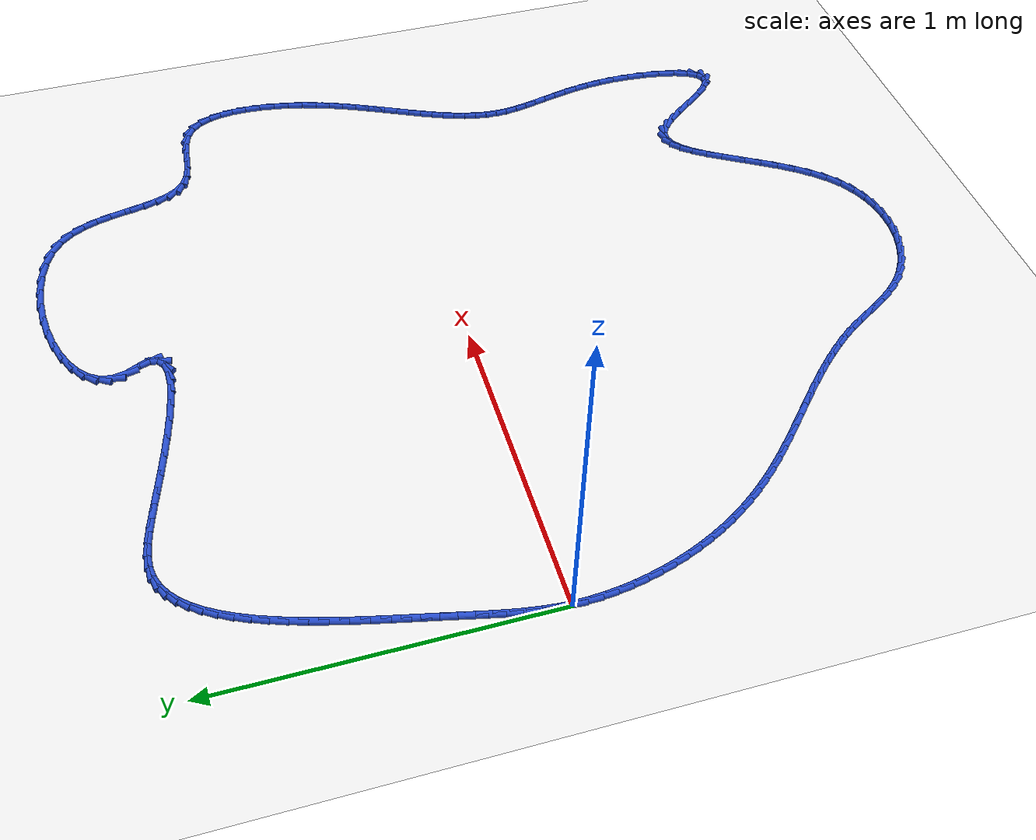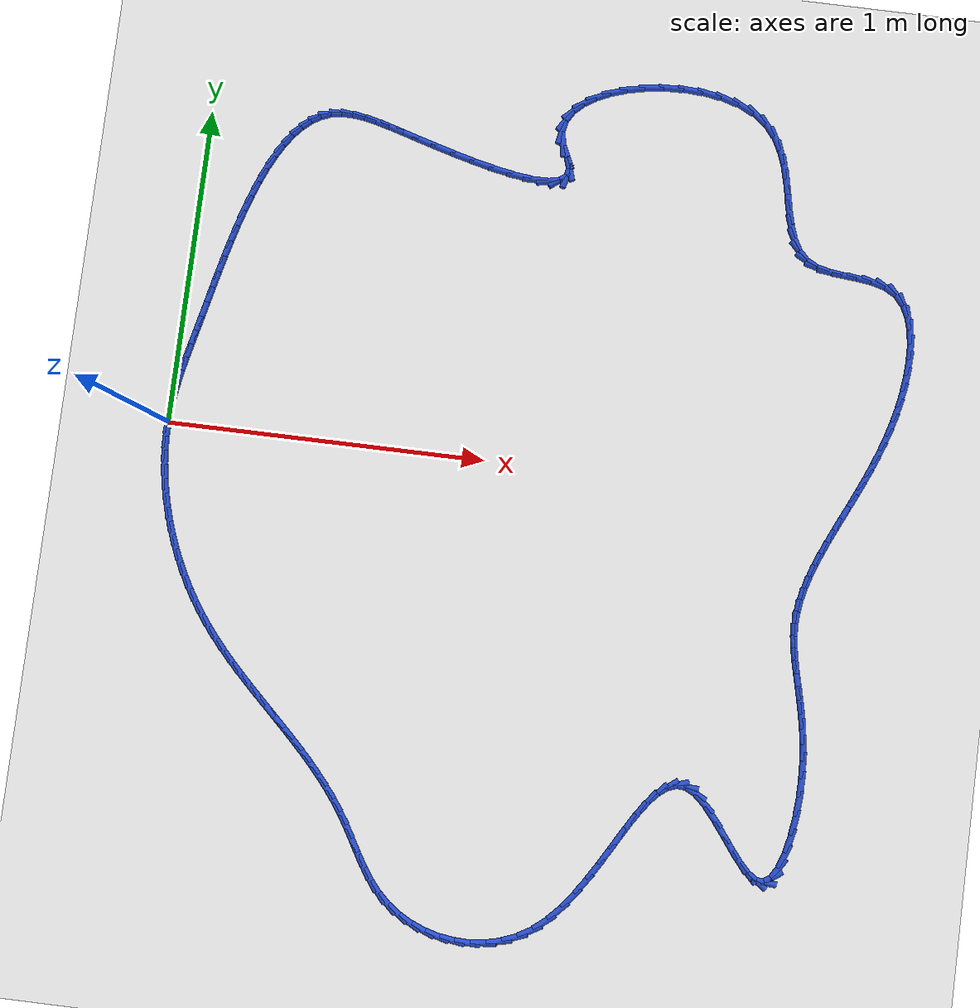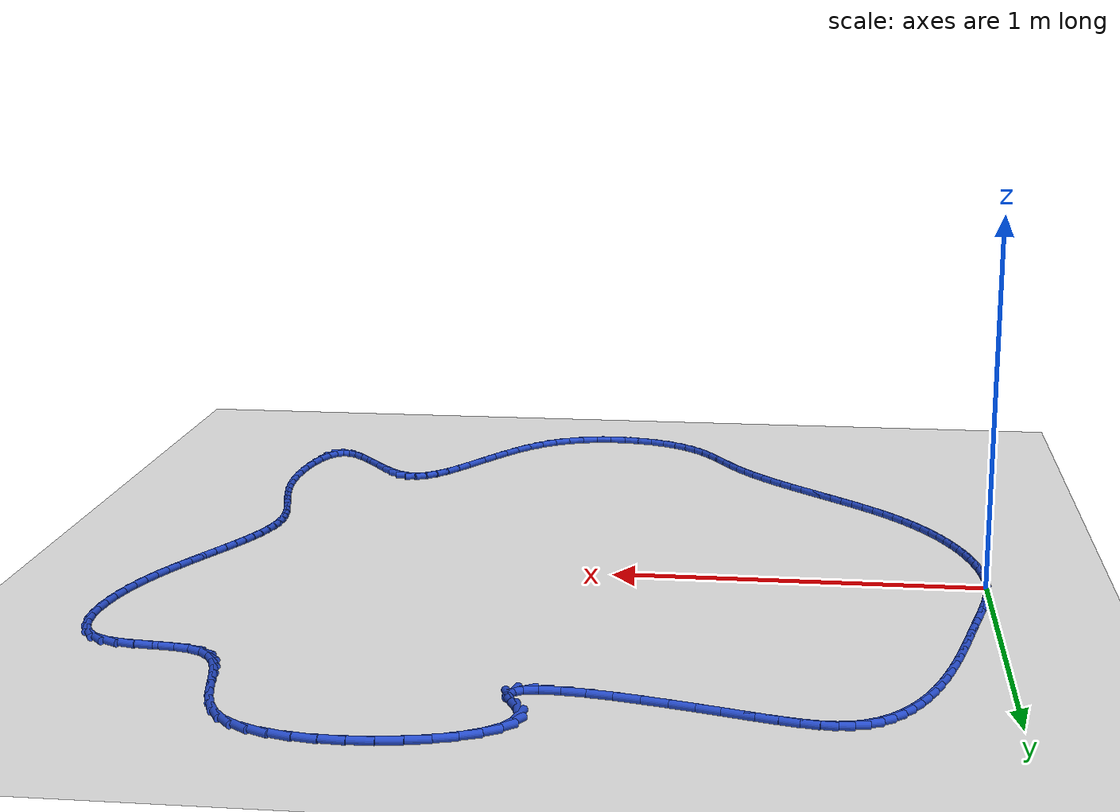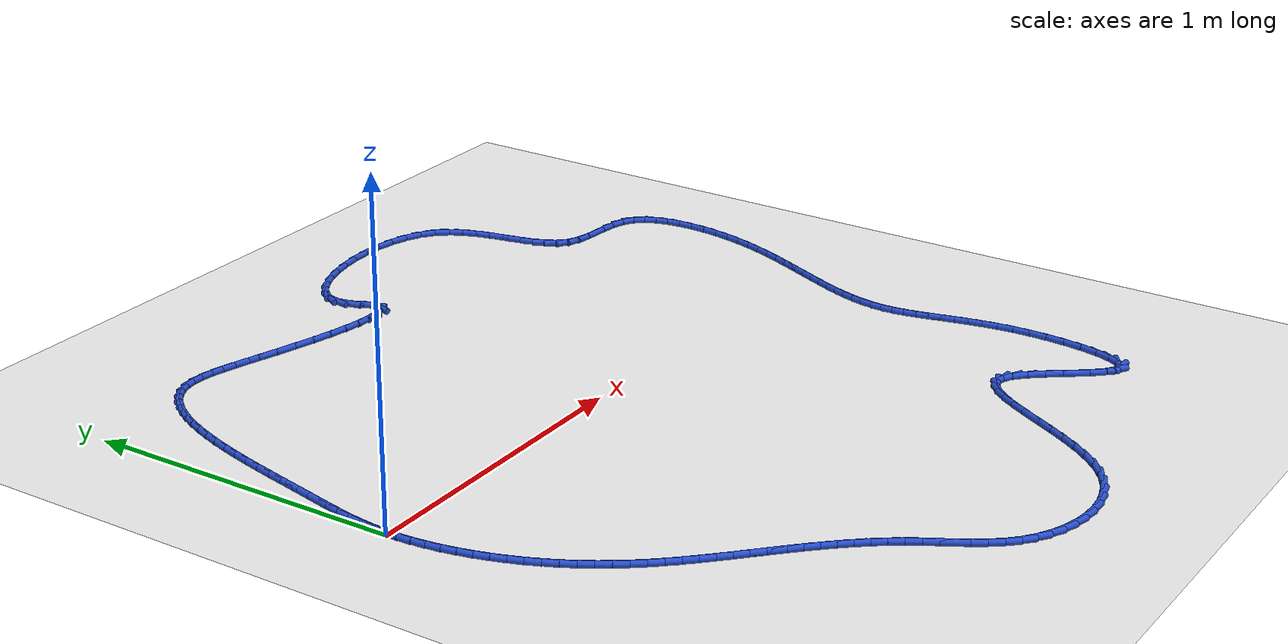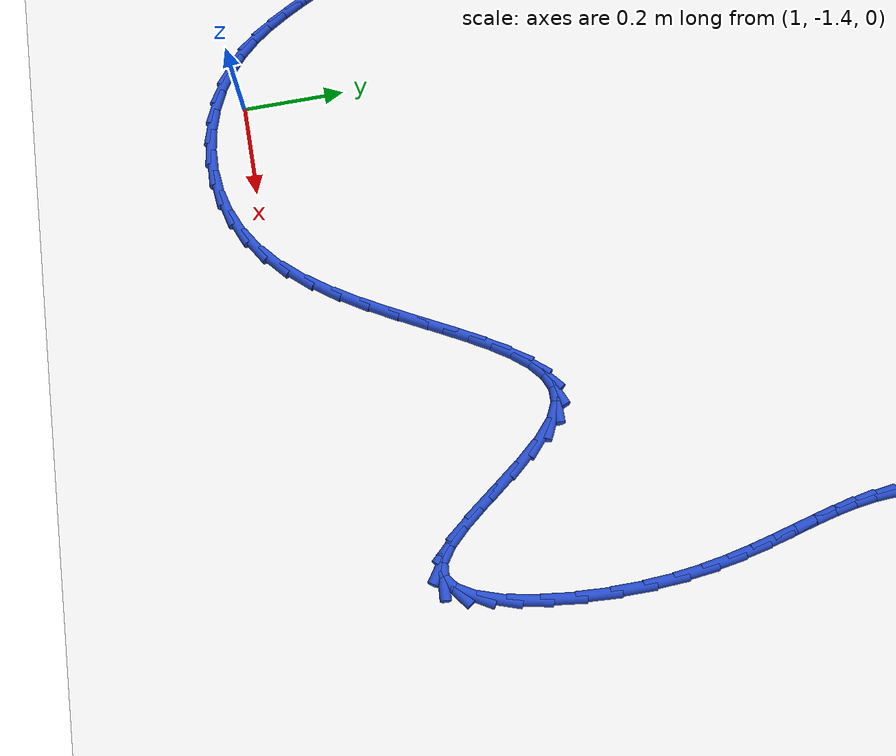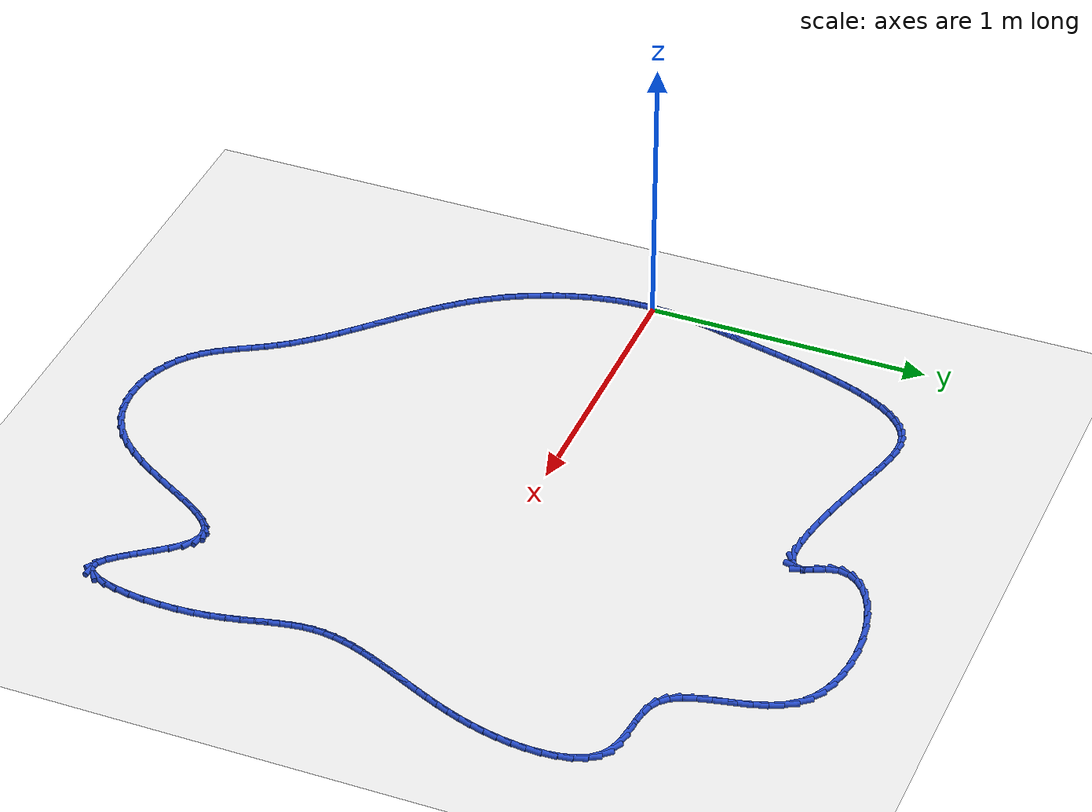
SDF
<sdf version="1.6">
 <world name="default">
  <light name="sun" type="directional">
   <pose>0 0 10 0 -0 0</pose>
   <diffuse>0.8 0.8 0.8 1</diffuse>
   <specular>0.2 0.2 0.2 1</specular>
   <attenuation>
    <range>1000</range>
    <constant>0.9</constant>
    <linear>0.01</linear>
    <quadratic>0.001</quadratic>
   </attenuation>
   <direction>-0.5 0.1 -0.9</direction>
  </light>
  <model name="ground_plane">
   <static>1</static>
   <link name="link">
    <collision name="collision">
     <geometry><plane><normal>0 0 1</normal><size>100 100</size></plane></geometry>
     <surface><friction><ode><mu>100</mu><mu2>50</mu2></ode></friction></surface>
    </collision>
    <visual name="visual">
     <cast_shadows>0</cast_shadows>
     <geometry><plane><normal>0 0 1</normal><size>100 100</size></plane></geometry>
     <material>
      <script><uri>file://media/materials/scripts/gazebo.material</uri><name>Gazebo/WhiteGlow</name></script>
     </material>
    </visual>
   </link>
  </model>
  <gravity>0 0 -9.8</gravity>
  <magnetic_field>6e-06 2.3e-05 -4.2e-05</magnetic_field>
  <atmosphere type="adiabatic"/>
  <physics name="default_physics" default="0" type="ode">
   <max_step_size>0.001</max_step_size>
   <real_time_factor>1</real_time_factor>
   <real_time_update_rate>1000</real_time_update_rate>
  </physics>
  <scene><ambient>0.4 0.4 0.4 1</ambient><background>0.7 0.7 0.7 1</background><shadows>1</shadows></scene>
  <spherical_coordinates>
   <surface_model>EARTH_WGS84</surface_model>
   <latitude_deg>0</latitude_deg>
   <longitude_deg>0</longitude_deg>
   <elevation>0</elevation>
   <heading_deg>0</heading_deg>
  </spherical_coordinates>
  <model name="line">
   <link name="link_0">
    <pose>8.673617379884035e-18 1.1102230246251565e-16 0.01 0 1.57 1.5194249731132563</pose>
    <collision name="collision">
     <geometry><cylinder><radius>0.01</radius><length>0.08</length></cylinder></geometry>
    </collision>
    <visual name="visual">
     <material>
      <script><name>Gazebo/Blue</name><uri>file://media/materials/scripts/gazebo.material</uri></script>
     </material>
     <geometry><cylinder><radius>0.01</radius><length>0.08</length></cylinder></geometry>
    </visual>
   </link>
   <link name="link_1">
    <pose>0.002190942777589316 0.042611591296382964 0.01 0 1.57 1.4687383677369295</pose>
    <collision name="collision">
     <geometry><cylinder><radius>0.01</radius><length>0.08</length></cylinder></geometry>
    </collision>
    <visual name="visual">
     <material>
      <script><name>Gazebo/Blue</name><uri>file://media/materials/scripts/gazebo.material</uri></script>
     </material>
     <geometry><cylinder><radius>0.01</radius><length>0.08</length></cylinder></geometry>
    </visual>
   </link>
   <link name="link_2">
    <pose>0.006519865810170455 0.08488054174759449 0.01 0 1.57 1.4261699032692958</pose>
    <collision name="collision">
     <geometry><cylinder><radius>0.01</radius><length>0.08</length></cylinder></geometry>
    </collision>
    <visual name="visual">
     <material>
      <script><name>Gazebo/Blue</name><uri>file://media/materials/scripts/gazebo.material</uri></script>
     </material>
     <geometry><cylinder><radius>0.01</radius><length>0.08</length></cylinder></geometry>
    </visual>
   </link>
   <link name="link_3">
    <pose>0.012678690763863158 0.1271675860584406 0.01 0 1.57 1.3926854214284805</pose>
    <collision name="collision">
     <geometry><cylinder><radius>0.01</radius><length>0.08</length></cylinder></geometry>
    </collision>
    <visual name="visual">
     <material>
      <script><name>Gazebo/Blue</name><uri>file://media/materials/scripts/gazebo.material</uri></script>
     </material>
     <geometry><cylinder><radius>0.01</radius><length>0.08</length></cylinder></geometry>
    </visual>
   </link>
   <link name="link_4">
    <pose>0.020359339304787193 0.1698334589337274 0.01 0 1.57 1.3686799920199342</pose>
    <collision name="collision">
     <geometry><cylinder><radius>0.01</radius><length>0.08</length></cylinder></geometry>
    </collision>
    <visual name="visual">
     <material>
      <script><name>Gazebo/Blue</name><uri>file://media/materials/scripts/gazebo.material</uri></script>
     </material>
     <geometry><cylinder><radius>0.01</radius><length>0.08</length></cylinder></geometry>
    </visual>
   </link>
   <link name="link_5">
    <pose>0.02925373309906229 0.2132388950782607 0.01 0 1.57 1.354057447493396</pose>
    <collision name="collision">
     <geometry><cylinder><radius>0.01</radius><length>0.08</length></cylinder></geometry>
    </collision>
    <visual name="visual">
     <material>
      <script><name>Gazebo/Blue</name><uri>file://media/materials/scripts/gazebo.material</uri></script>
     </material>
     <geometry><cylinder><radius>0.01</radius><length>0.08</length></cylinder></geometry>
    </visual>
   </link>
   <link name="link_6">
    <pose>0.03905379381280821 0.25774462919684654 0.01 0 1.57 1.348340691334399</pose>
    <collision name="collision">
     <geometry><cylinder><radius>0.01</radius><length>0.08</length></cylinder></geometry>
    </collision>
    <visual name="visual">
     <material>
      <script><name>Gazebo/Blue</name><uri>file://media/materials/scripts/gazebo.material</uri></script>
     </material>
     <geometry><cylinder><radius>0.01</radius><length>0.08</length></cylinder></geometry>
    </visual>
   </link>
   <link name="link_7">
    <pose>0.04945144311214468 0.30371139599429076 0.01 0 1.57 1.3504304282927446</pose>
    <collision name="collision">
     <geometry><cylinder><radius>0.01</radius><length>0.08</length></cylinder></geometry>
    </collision>
    <visual name="visual">
     <material>
      <script><name>Gazebo/Blue</name><uri>file://media/materials/scripts/gazebo.material</uri></script>
     </material>
     <geometry><cylinder><radius>0.01</radius><length>0.08</length></cylinder></geometry>
    </visual>
   </link>
   <link name="link_8">
    <pose>0.06015090043293852 0.3514760524809787 0.01 0 1.57 1.3534257557211442</pose>
    <collision name="collision">
     <geometry><cylinder><radius>0.01</radius><length>0.08</length></cylinder></geometry>
    </collision>
    <visual name="visual">
     <material>
      <script><name>Gazebo/Blue</name><uri>file://media/materials/scripts/gazebo.material</uri></script>
     </material>
     <geometry><cylinder><radius>0.01</radius><length>0.08</length></cylinder></geometry>
    </visual>
   </link>
   <link name="link_9">
    <pose>0.07107705800835572 0.4009469911790704 0.01 0 1.57 1.3521545960017007</pose>
    <collision name="collision">
     <geometry><cylinder><radius>0.01</radius><length>0.08</length></cylinder></geometry>
    </collision>
    <visual name="visual">
     <material>
      <script><name>Gazebo/Blue</name><uri>file://media/materials/scripts/gazebo.material</uri></script>
     </material>
     <geometry><cylinder><radius>0.01</radius><length>0.08</length></cylinder></geometry>
    </visual>
   </link>
   <link name="link_10">
    <pose>0.08234563257996456 0.4516620943968097 0.01 0 1.57 1.346731115510854</pose>
    <collision name="collision">
     <geometry><cylinder><radius>0.01</radius><length>0.08</length></cylinder></geometry>
    </collision>
    <visual name="visual">
     <material>
      <script><name>Gazebo/Blue</name><uri>file://media/materials/scripts/gazebo.material</uri></script>
     </material>
     <geometry><cylinder><radius>0.01</radius><length>0.08</length></cylinder></geometry>
    </visual>
   </link>
   <link name="link_11">
    <pose>0.09407862945060337 0.5031470343956221 0.01 0 1.57 1.3372222786992882</pose>
    <collision name="collision">
     <geometry><cylinder><radius>0.01</radius><length>0.08</length></cylinder></geometry>
    </collision>
    <visual name="visual">
     <material>
      <script><name>Gazebo/Blue</name><uri>file://media/materials/scripts/gazebo.material</uri></script>
     </material>
     <geometry><cylinder><radius>0.01</radius><length>0.08</length></cylinder></geometry>
    </visual>
   </link>
   <link name="link_12">
    <pose>0.10639805392311062 0.5549274834369342 0.01 0 1.57 1.323494425854062</pose>
    <collision name="collision">
     <geometry><cylinder><radius>0.01</radius><length>0.08</length></cylinder></geometry>
    </collision>
    <visual name="visual">
     <material>
      <script><name>Gazebo/Blue</name><uri>file://media/materials/scripts/gazebo.material</uri></script>
     </material>
     <geometry><cylinder><radius>0.01</radius><length>0.08</length></cylinder></geometry>
    </visual>
   </link>
   <link name="link_13">
    <pose>0.11942591130032462 0.6065291137821713 0.01 0 1.57 1.3052156974553881</pose>
    <collision name="collision">
     <geometry><cylinder><radius>0.01</radius><length>0.08</length></cylinder></geometry>
    </collision>
    <visual name="visual">
     <material>
      <script><name>Gazebo/Blue</name><uri>file://media/materials/scripts/gazebo.material</uri></script>
     </material>
     <geometry><cylinder><radius>0.01</radius><length>0.08</length></cylinder></geometry>
    </visual>
   </link>
   <link name="link_14">
    <pose>0.1332842068850838 0.6574775976927597 0.01 0 1.57 1.281837744129562</pose>
    <collision name="collision">
     <geometry><cylinder><radius>0.01</radius><length>0.08</length></cylinder></geometry>
    </collision>
    <visual name="visual">
     <material>
      <script><name>Gazebo/Blue</name><uri>file://media/materials/scripts/gazebo.material</uri></script>
     </material>
     <geometry><cylinder><radius>0.01</radius><length>0.08</length></cylinder></geometry>
    </visual>
   </link>
   <link name="link_15">
    <pose>0.1480949459802266 0.7072986074301257 0.01 0 1.57 1.252556622742605</pose>
    <collision name="collision">
     <geometry><cylinder><radius>0.01</radius><length>0.08</length></cylinder></geometry>
    </collision>
    <visual name="visual">
     <material>
      <script><name>Gazebo/Blue</name><uri>file://media/materials/scripts/gazebo.material</uri></script>
     </material>
     <geometry><cylinder><radius>0.01</radius><length>0.08</length></cylinder></geometry>
    </visual>
   </link>
   <link name="link_16">
    <pose>0.16398013388859134 0.7555178152556951 0.01 0 1.57 1.2162505183375831</pose>
    <collision name="collision">
     <geometry><cylinder><radius>0.01</radius><length>0.08</length></cylinder></geometry>
    </collision>
    <visual name="visual">
     <material>
      <script><name>Gazebo/Blue</name><uri>file://media/materials/scripts/gazebo.material</uri></script>
     </material>
     <geometry><cylinder><radius>0.01</radius><length>0.08</length></cylinder></geometry>
    </visual>
   </link>
   <link name="link_17">
    <pose>0.18106177591301653 0.8016608934308941 0.01 0 1.57 1.171391261262714</pose>
    <collision name="collision">
     <geometry><cylinder><radius>0.01</radius><length>0.08</length></cylinder></geometry>
    </collision>
    <visual name="visual">
     <material>
      <script><name>Gazebo/Blue</name><uri>file://media/materials/scripts/gazebo.material</uri></script>
     </material>
     <geometry><cylinder><radius>0.01</radius><length>0.08</length></cylinder></geometry>
    </visual>
   </link>
   <link name="link_18">
    <pose>0.19946187735634047 0.8452535142171483 0.01 0 1.57 1.1159297989686674</pose>
    <collision name="collision">
     <geometry><cylinder><radius>0.01</radius><length>0.08</length></cylinder></geometry>
    </collision>
    <visual name="visual">
     <material>
      <script><name>Gazebo/Blue</name><uri>file://media/materials/scripts/gazebo.material</uri></script>
     </material>
     <geometry><cylinder><radius>0.01</radius><length>0.08</length></cylinder></geometry>
    </visual>
   </link>
   <link name="link_19">
    <pose>0.2193024435214015 0.8858213498758838 0.01 0 1.57 1.0471692439644458</pose>
    <collision name="collision">
     <geometry><cylinder><radius>0.01</radius><length>0.08</length></cylinder></geometry>
    </collision>
    <visual name="visual">
     <material>
      <script><name>Gazebo/Blue</name><uri>file://media/materials/scripts/gazebo.material</uri></script>
     </material>
     <geometry><cylinder><radius>0.01</radius><length>0.08</length></cylinder></geometry>
    </visual>
   </link>
   <link name="link_20">
    <pose>0.24070547971103817 0.9228900726685271 0.01 0 1.57 0.9616779853916648</pose>
    <collision name="collision">
     <geometry><cylinder><radius>0.01</radius><length>0.08</length></cylinder></geometry>
    </collision>
    <visual name="visual">
     <material>
      <script><name>Gazebo/Blue</name><uri>file://media/materials/scripts/gazebo.material</uri></script>
     </material>
     <geometry><cylinder><radius>0.01</radius><length>0.08</length></cylinder></geometry>
    </visual>
   </link>
   <link name="link_21">
    <pose>0.2637929912280888 0.9559853548565036 0.01 0 1.57 0.8553885485651384</pose>
    <collision name="collision">
     <geometry><cylinder><radius>0.01</radius><length>0.08</length></cylinder></geometry>
    </collision>
    <visual name="visual">
     <material>
      <script><name>Gazebo/Blue</name><uri>file://media/materials/scripts/gazebo.material</uri></script>
     </material>
     <geometry><cylinder><radius>0.01</radius><length>0.08</length></cylinder></geometry>
    </visual>
   </link>
   <link name="link_22">
    <pose>0.2886869833753918 0.9846328687012398 0.01 0 1.57 0.7242048431492434</pose>
    <collision name="collision">
     <geometry><cylinder><radius>0.01</radius><length>0.08</length></cylinder></geometry>
    </collision>
    <visual name="visual">
     <material>
      <script><name>Gazebo/Blue</name><uri>file://media/materials/scripts/gazebo.material</uri></script>
     </material>
     <geometry><cylinder><radius>0.01</radius><length>0.08</length></cylinder></geometry>
    </visual>
   </link>
   <link name="link_23">
    <pose>0.3155094614557855 1.0083582864641614 0.01 0 1.57 0.5656261777214222</pose>
    <collision name="collision">
     <geometry><cylinder><radius>0.01</radius><length>0.08</length></cylinder></geometry>
    </collision>
    <visual name="visual">
     <material>
      <script><name>Gazebo/Blue</name><uri>file://media/materials/scripts/gazebo.material</uri></script>
     </material>
     <geometry><cylinder><radius>0.01</radius><length>0.08</length></cylinder></geometry>
    </visual>
   </link>
   <link name="link_24">
    <pose>0.3443824307721084 1.0266872804066944 0.01 0 1.57 0.38161815619963496</pose>
    <collision name="collision">
     <geometry><cylinder><radius>0.01</radius><length>0.08</length></cylinder></geometry>
    </collision>
    <visual name="visual">
     <material>
      <script><name>Gazebo/Blue</name><uri>file://media/materials/scripts/gazebo.material</uri></script>
     </material>
     <geometry><cylinder><radius>0.01</radius><length>0.08</length></cylinder></geometry>
    </visual>
   </link>
   <link name="link_25">
    <pose>0.37542789662719867 1.039145522790265 0.01 0 1.57 0.18335152184600492</pose>
    <collision name="collision">
     <geometry><cylinder><radius>0.01</radius><length>0.08</length></cylinder></geometry>
    </collision>
    <visual name="visual">
     <material>
      <script><name>Gazebo/Blue</name><uri>file://media/materials/scripts/gazebo.material</uri></script>
     </material>
     <geometry><cylinder><radius>0.01</radius><length>0.08</length></cylinder></geometry>
    </visual>
   </link>
   <link name="link_26">
    <pose>0.40878972322557533 1.0453319449310285 0.01 0 1.57 0.0078222710358069</pose>
    <collision name="collision">
     <geometry><cylinder><radius>0.01</radius><length>0.08</length></cylinder></geometry>
    </collision>
    <visual name="visual">
     <material>
      <script><name>Gazebo/Blue</name><uri>file://media/materials/scripts/gazebo.material</uri></script>
     </material>
     <geometry><cylinder><radius>0.01</radius><length>0.08</length></cylinder></geometry>
    </visual>
   </link>
   <link name="link_27">
    <pose>0.4448410712097215 1.045613954098042 0.01 0 1.57 -0.12158621610724099</pose>
    <collision name="collision">
     <geometry><cylinder><radius>0.01</radius><length>0.08</length></cylinder></geometry>
    </collision>
    <visual name="visual">
     <material>
      <script><name>Gazebo/Blue</name><uri>file://media/materials/scripts/gazebo.material</uri></script>
     </material>
     <geometry><cylinder><radius>0.01</radius><length>0.08</length></cylinder></geometry>
    </visual>
   </link>
   <link name="link_28">
    <pose>0.48409204551058005 1.0408179197383294 0.01 0 1.57 -0.20742512681563874</pose>
    <collision name="collision">
     <geometry><cylinder><radius>0.01</radius><length>0.08</length></cylinder></geometry>
    </collision>
    <visual name="visual">
     <material>
      <script><name>Gazebo/Blue</name><uri>file://media/materials/scripts/gazebo.material</uri></script>
     </material>
     <geometry><cylinder><radius>0.01</radius><length>0.08</length></cylinder></geometry>
    </visual>
   </link>
   <link name="link_29">
    <pose>0.5270545869305834 1.0317763641336664 0.01 0 1.57 -0.25806034854803295</pose>
    <collision name="collision">
     <geometry><cylinder><radius>0.01</radius><length>0.08</length></cylinder></geometry>
    </collision>
    <visual name="visual">
     <material>
      <script><name>Gazebo/Blue</name><uri>file://media/materials/scripts/gazebo.material</uri></script>
     </material>
     <geometry><cylinder><radius>0.01</radius><length>0.08</length></cylinder></geometry>
    </visual>
   </link>
   <link name="link_30">
    <pose>0.5742406362721629 1.019321809565829 0.01 0 1.57 -0.28186292065076246</pose>
    <collision name="collision">
     <geometry><cylinder><radius>0.01</radius><length>0.08</length></cylinder></geometry>
    </collision>
    <visual name="visual">
     <material>
      <script><name>Gazebo/Blue</name><uri>file://media/materials/scripts/gazebo.material</uri></script>
     </material>
     <geometry><cylinder><radius>0.01</radius><length>0.08</length></cylinder></geometry>
    </visual>
   </link>
   <link name="link_31">
    <pose>0.6261621343377513 1.0042867783165927 0.01 0 1.57 -0.285642556510455</pose>
    <collision name="collision">
     <geometry><cylinder><radius>0.01</radius><length>0.08</length></cylinder></geometry>
    </collision>
    <visual name="visual">
     <material>
      <script><name>Gazebo/Blue</name><uri>file://media/materials/scripts/gazebo.material</uri></script>
     </material>
     <geometry><cylinder><radius>0.01</radius><length>0.08</length></cylinder></geometry>
    </visual>
   </link>
   <link name="link_32">
    <pose>0.6833004544550433 0.9875067710316887 0.01 0 1.57 -0.277534522926929</pose>
    <collision name="collision">
     <geometry><cylinder><radius>0.01</radius><length>0.08</length></cylinder></geometry>
    </collision>
    <visual name="visual">
     <material>
      <script><name>Gazebo/Blue</name><uri>file://media/materials/scripts/gazebo.material</uri></script>
     </material>
     <geometry><cylinder><radius>0.01</radius><length>0.08</length></cylinder></geometry>
    </visual>
   </link>
   <link name="link_33">
    <pose>0.7450069925418794 0.9699273885210464 0.01 0 1.57 -0.2631560042710093</pose>
    <collision name="collision">
     <geometry><cylinder><radius>0.01</radius><length>0.08</length></cylinder></geometry>
    </collision>
    <visual name="visual">
     <material>
      <script><name>Gazebo/Blue</name><uri>file://media/materials/scripts/gazebo.material</uri></script>
     </material>
     <geometry><cylinder><radius>0.01</radius><length>0.08</length></cylinder></geometry>
    </visual>
   </link>
   <link name="link_34">
    <pose>0.8091981462610565 0.9526340516849137 0.01 0 1.57 -0.24188227856018582</pose>
    <collision name="collision">
     <geometry><cylinder><radius>0.01</radius><length>0.08</length></cylinder></geometry>
    </collision>
    <visual name="visual">
     <material>
      <script><name>Gazebo/Blue</name><uri>file://media/materials/scripts/gazebo.material</uri></script>
     </material>
     <geometry><cylinder><radius>0.01</radius><length>0.08</length></cylinder></geometry>
    </visual>
   </link>
   <link name="link_35">
    <pose>0.8736976475123334 0.9367212103790179 0.01 0 1.57 -0.21135043329230913</pose>
    <collision name="collision">
     <geometry><cylinder><radius>0.01</radius><length>0.08</length></cylinder></geometry>
    </collision>
    <visual name="visual">
     <material>
      <script><name>Gazebo/Blue</name><uri>file://media/materials/scripts/gazebo.material</uri></script>
     </material>
     <geometry><cylinder><radius>0.01</radius><length>0.08</length></cylinder></geometry>
    </visual>
   </link>
   <link name="link_36">
    <pose>0.9363292281954696 0.9232833144590866 0.01 0 1.57 -0.16687425508155795</pose>
    <collision name="collision">
     <geometry><cylinder><radius>0.01</radius><length>0.08</length></cylinder></geometry>
    </collision>
    <visual name="visual">
     <material>
      <script><name>Gazebo/Blue</name><uri>file://media/materials/scripts/gazebo.material</uri></script>
     </material>
     <geometry><cylinder><radius>0.01</radius><length>0.08</length></cylinder></geometry>
    </visual>
   </link>
   <link name="link_37">
    <pose>0.9949166202102242 0.9134148137808471 0.01 0 1.57 -0.09906287607964231</pose>
    <collision name="collision">
     <geometry><cylinder><radius>0.01</radius><length>0.08</length></cylinder></geometry>
    </collision>
    <visual name="visual">
     <material>
      <script><name>Gazebo/Blue</name><uri>file://media/materials/scripts/gazebo.material</uri></script>
     </material>
     <geometry><cylinder><radius>0.01</radius><length>0.08</length></cylinder></geometry>
    </visual>
   </link>
   <link name="link_38">
    <pose>1.0472835554563564 0.9082101582000266 0.01 0 1.57 0.012590572401151719</pose>
    <collision name="collision">
     <geometry><cylinder><radius>0.01</radius><length>0.08</length></cylinder></geometry>
    </collision>
    <visual name="visual">
     <material>
      <script><name>Gazebo/Blue</name><uri>file://media/materials/scripts/gazebo.material</uri></script>
     </material>
     <geometry><cylinder><radius>0.01</radius><length>0.08</length></cylinder></geometry>
    </visual>
   </link>
   <link name="link_39">
    <pose>1.091253765833626 0.9087637975723529 0.01 0 1.57 0.2182346322781759</pose>
    <collision name="collision">
     <geometry><cylinder><radius>0.01</radius><length>0.08</length></cylinder></geometry>
    </collision>
    <visual name="visual">
     <material>
      <script><name>Gazebo/Blue</name><uri>file://media/materials/scripts/gazebo.material</uri></script>
     </material>
     <geometry><cylinder><radius>0.01</radius><length>0.08</length></cylinder></geometry>
    </visual>
   </link>
   <link name="link_40">
    <pose>1.1246509832417912 0.9161701817535526 0.01 0 1.57 0.6393849790030512</pose>
    <collision name="collision">
     <geometry><cylinder><radius>0.01</radius><length>0.08</length></cylinder></geometry>
    </collision>
    <visual name="visual">
     <material>
      <script><name>Gazebo/Blue</name><uri>file://media/materials/scripts/gazebo.material</uri></script>
     </material>
     <geometry><cylinder><radius>0.01</radius><length>0.08</length></cylinder></geometry>
    </visual>
   </link>
   <link name="link_41">
    <pose>1.1452989395806117 0.9315237605993534 0.01 0 1.57 1.340390361876612</pose>
    <collision name="collision">
     <geometry><cylinder><radius>0.01</radius><length>0.08</length></cylinder></geometry>
    </collision>
    <visual name="visual">
     <material>
      <script><name>Gazebo/Blue</name><uri>file://media/materials/scripts/gazebo.material</uri></script>
     </material>
     <geometry><cylinder><radius>0.01</radius><length>0.08</length></cylinder></geometry>
    </visual>
   </link>
   <link name="link_42">
    <pose>1.151021366749847 0.9559189839654828 0.01 0 1.57 -1.2582821820882537</pose>
    <collision name="collision">
     <geometry><cylinder><radius>0.01</radius><length>0.08</length></cylinder></geometry>
    </collision>
    <visual name="visual">
     <material>
      <script><name>Gazebo/Blue</name><uri>file://media/materials/scripts/gazebo.material</uri></script>
     </material>
     <geometry><cylinder><radius>0.01</radius><length>0.08</length></cylinder></geometry>
    </visual>
   </link>
   <link name="link_43">
    <pose>1.139897186151034 0.990348313481829 0.01 0 1.57 -1.1331733186361472</pose>
    <collision name="collision">
     <geometry><cylinder><radius>0.01</radius><length>0.08</length></cylinder></geometry>
    </collision>
    <visual name="visual">
     <material>
      <script><name>Gazebo/Blue</name><uri>file://media/materials/scripts/gazebo.material</uri></script>
     </material>
     <geometry><cylinder><radius>0.01</radius><length>0.08</length></cylinder></geometry>
    </visual>
   </link>
   <link name="link_44">
    <pose>1.1206127888355242 1.031564863145676 0.01 0 1.57 -1.3776159690278627</pose>
    <collision name="collision">
     <geometry><cylinder><radius>0.01</radius><length>0.08</length></cylinder></geometry>
    </collision>
    <visual name="visual">
     <material>
      <script><name>Gazebo/Blue</name><uri>file://media/materials/scripts/gazebo.material</uri></script>
     </material>
     <geometry><cylinder><radius>0.01</radius><length>0.08</length></cylinder></geometry>
    </visual>
   </link>
   <link name="link_45">
    <pose>1.1127396175747555 1.0718121642143739 0.01 0 1.57 1.3802352312611053</pose>
    <collision name="collision">
     <geometry><cylinder><radius>0.01</radius><length>0.08</length></cylinder></geometry>
    </collision>
    <visual name="visual">
     <material>
      <script><name>Gazebo/Blue</name><uri>file://media/materials/scripts/gazebo.material</uri></script>
     </material>
     <geometry><cylinder><radius>0.01</radius><length>0.08</length></cylinder></geometry>
    </visual>
   </link>
   <link name="link_46">
    <pose>1.1198927889993353 1.1088941059618003 0.01 0 1.57 1.0259331059388677</pose>
    <collision name="collision">
     <geometry><cylinder><radius>0.01</radius><length>0.08</length></cylinder></geometry>
    </collision>
    <visual name="visual">
     <material>
      <script><name>Gazebo/Blue</name><uri>file://media/materials/scripts/gazebo.material</uri></script>
     </material>
     <geometry><cylinder><radius>0.01</radius><length>0.08</length></cylinder></geometry>
    </visual>
   </link>
   <link name="link_47">
    <pose>1.1402710297754832 1.1425182559331322 0.01 0 1.57 0.7541980252064904</pose>
    <collision name="collision">
     <geometry><cylinder><radius>0.01</radius><length>0.08</length></cylinder></geometry>
    </collision>
    <visual name="visual">
     <material>
      <script><name>Gazebo/Blue</name><uri>file://media/materials/scripts/gazebo.material</uri></script>
     </material>
     <geometry><cylinder><radius>0.01</radius><length>0.08</length></cylinder></geometry>
    </visual>
   </link>
   <link name="link_48">
    <pose>1.1720706718927707 1.172393023321573 0.01 0 1.57 0.557694824736903</pose>
    <collision name="collision">
     <geometry><cylinder><radius>0.01</radius><length>0.08</length></cylinder></geometry>
    </collision>
    <visual name="visual">
     <material>
      <script><name>Gazebo/Blue</name><uri>file://media/materials/scripts/gazebo.material</uri></script>
     </material>
     <geometry><cylinder><radius>0.01</radius><length>0.08</length></cylinder></geometry>
    </visual>
   </link>
   <link name="link_49">
    <pose>1.2134880473407668 1.198226817320323 0.01 0 1.57 0.41177049169611074</pose>
    <collision name="collision">
     <geometry><cylinder><radius>0.01</radius><length>0.08</length></cylinder></geometry>
    </collision>
    <visual name="visual">
     <material>
      <script><name>Gazebo/Blue</name><uri>file://media/materials/scripts/gazebo.material</uri></script>
     </material>
     <geometry><cylinder><radius>0.01</radius><length>0.08</length></cylinder></geometry>
    </visual>
   </link>
   <link name="link_50">
    <pose>1.2627194881090427 1.219728047122585 0.01 0 1.57 0.2965064750438356</pose>
    <collision name="collision">
     <geometry><cylinder><radius>0.01</radius><length>0.08</length></cylinder></geometry>
    </collision>
    <visual name="visual">
     <material>
      <script><name>Gazebo/Blue</name><uri>file://media/materials/scripts/gazebo.material</uri></script>
     </material>
     <geometry><cylinder><radius>0.01</radius><length>0.08</length></cylinder></geometry>
    </visual>
   </link>
   <link name="link_51">
    <pose>1.3179613261871679 1.2366051219215604 0.01 0 1.57 0.19855362124217077</pose>
    <collision name="collision">
     <geometry><cylinder><radius>0.01</radius><length>0.08</length></cylinder></geometry>
    </collision>
    <visual name="visual">
     <material>
      <script><name>Gazebo/Blue</name><uri>file://media/materials/scripts/gazebo.material</uri></script>
     </material>
     <geometry><cylinder><radius>0.01</radius><length>0.08</length></cylinder></geometry>
    </visual>
   </link>
   <link name="link_52">
    <pose>1.3774098935647132 1.2485664509104515 0.01 0 1.57 0.10876573950773355</pose>
    <collision name="collision">
     <geometry><cylinder><radius>0.01</radius><length>0.08</length></cylinder></geometry>
    </collision>
    <visual name="visual">
     <material>
      <script><name>Gazebo/Blue</name><uri>file://media/materials/scripts/gazebo.material</uri></script>
     </material>
     <geometry><cylinder><radius>0.01</radius><length>0.08</length></cylinder></geometry>
    </visual>
   </link>
   <link name="link_53">
    <pose>1.439261522231247 1.255320443282459 0.01 0 1.57 0.02009408308451766</pose>
    <collision name="collision">
     <geometry><cylinder><radius>0.01</radius><length>0.08</length></cylinder></geometry>
    </collision>
    <visual name="visual">
     <material>
      <script><name>Gazebo/Blue</name><uri>file://media/materials/scripts/gazebo.material</uri></script>
     </material>
     <geometry><cylinder><radius>0.01</radius><length>0.08</length></cylinder></geometry>
    </visual>
   </link>
   <link name="link_54">
    <pose>1.5017125441763417 1.2565755082307852 0.01 0 1.57 -0.0739172327099798</pose>
    <collision name="collision">
     <geometry><cylinder><radius>0.01</radius><length>0.08</length></cylinder></geometry>
    </collision>
    <visual name="visual">
     <material>
      <script><name>Gazebo/Blue</name><uri>file://media/materials/scripts/gazebo.material</uri></script>
     </material>
     <geometry><cylinder><radius>0.01</radius><length>0.08</length></cylinder></geometry>
    </visual>
   </link>
   <link name="link_55">
    <pose>1.5629592913895667 1.2520400549486321 0.01 0 1.57 -0.18033030093902777</pose>
    <collision name="collision">
     <geometry><cylinder><radius>0.01</radius><length>0.08</length></cylinder></geometry>
    </collision>
    <visual name="visual">
     <material>
      <script><name>Gazebo/Blue</name><uri>file://media/materials/scripts/gazebo.material</uri></script>
     </material>
     <geometry><cylinder><radius>0.01</radius><length>0.08</length></cylinder></geometry>
    </visual>
   </link>
   <link name="link_56">
    <pose>1.621198095860491 1.2414224926292015 0.01 0 1.57 -0.30791171388644833</pose>
    <collision name="collision">
     <geometry><cylinder><radius>0.01</radius><length>0.08</length></cylinder></geometry>
    </collision>
    <visual name="visual">
     <material>
      <script><name>Gazebo/Blue</name><uri>file://media/materials/scripts/gazebo.material</uri></script>
     </material>
     <geometry><cylinder><radius>0.01</radius><length>0.08</length></cylinder></geometry>
    </visual>
   </link>
   <link name="link_57">
    <pose>1.6746252895786862 1.2244312304656946 0.01 0 1.57 -0.4679210229439961</pose>
    <collision name="collision">
     <geometry><cylinder><radius>0.01</radius><length>0.08</length></cylinder></geometry>
    </collision>
    <visual name="visual">
     <material>
      <script><name>Gazebo/Blue</name><uri>file://media/materials/scripts/gazebo.material</uri></script>
     </material>
     <geometry><cylinder><radius>0.01</radius><length>0.08</length></cylinder></geometry>
    </visual>
   </link>
   <link name="link_58">
    <pose>1.7214372045337218 1.2007746776513133 0.01 0 1.57 -0.6728107091520963</pose>
    <collision name="collision">
     <geometry><cylinder><radius>0.01</radius><length>0.08</length></cylinder></geometry>
    </collision>
    <visual name="visual">
     <material>
      <script><name>Gazebo/Blue</name><uri>file://media/materials/scripts/gazebo.material</uri></script>
     </material>
     <geometry><cylinder><radius>0.01</radius><length>0.08</length></cylinder></geometry>
    </visual>
   </link>
   <link name="link_59">
    <pose>1.7598456325187677 1.1701693329907057 0.01 0 1.57 -0.9011435893548</pose>
    <collision name="collision">
     <geometry><cylinder><radius>0.01</radius><length>0.08</length></cylinder></geometry>
    </collision>
    <visual name="visual">
     <material>
      <script><name>Gazebo/Blue</name><uri>file://media/materials/scripts/gazebo.material</uri></script>
     </material>
     <geometry><cylinder><radius>0.01</radius><length>0.08</length></cylinder></geometry>
    </visual>
   </link>
   <link name="link_60">
    <pose>1.7892919174192368 1.1329750798317935 0.01 0 1.57 -1.0908865986088185</pose>
    <collision name="collision">
     <geometry><cylinder><radius>0.01</radius><length>0.08</length></cylinder></geometry>
    </collision>
    <visual name="visual">
     <material>
      <script><name>Gazebo/Blue</name><uri>file://media/materials/scripts/gazebo.material</uri></script>
     </material>
     <geometry><cylinder><radius>0.01</radius><length>0.08</length></cylinder></geometry>
    </visual>
   </link>
   <link name="link_61">
    <pose>1.811320710841849 1.090652393913972 0.01 0 1.57 -1.228247749188316</pose>
    <collision name="collision">
     <geometry><cylinder><radius>0.01</radius><length>0.08</length></cylinder></geometry>
    </collision>
    <visual name="visual">
     <material>
      <script><name>Gazebo/Blue</name><uri>file://media/materials/scripts/gazebo.material</uri></script>
     </material>
     <geometry><cylinder><radius>0.01</radius><length>0.08</length></cylinder></geometry>
    </visual>
   </link>
   <link name="link_62">
    <pose>1.8276828242571124 1.0447696277153629 0.01 0 1.57 -1.3164502512299165</pose>
    <collision name="collision">
     <geometry><cylinder><radius>0.01</radius><length>0.08</length></cylinder></geometry>
    </collision>
    <visual name="visual">
     <material>
      <script><name>Gazebo/Blue</name><uri>file://media/materials/scripts/gazebo.material</uri></script>
     </material>
     <geometry><cylinder><radius>0.01</radius><length>0.08</length></cylinder></geometry>
    </visual>
   </link>
   <link name="link_63">
    <pose>1.8401290691355328 0.9968951337140868 0.01 0 1.57 -1.3610565429840256</pose>
    <collision name="collision">
     <geometry><cylinder><radius>0.01</radius><length>0.08</length></cylinder></geometry>
    </collision>
    <visual name="visual">
     <material>
      <script><name>Gazebo/Blue</name><uri>file://media/materials/scripts/gazebo.material</uri></script>
     </material>
     <geometry><cylinder><radius>0.01</radius><length>0.08</length></cylinder></geometry>
    </visual>
   </link>
   <link name="link_64">
    <pose>1.8504102569476186 0.948597264388264 0.01 0 1.57 -1.364518508799038</pose>
    <collision name="collision">
     <geometry><cylinder><radius>0.01</radius><length>0.08</length></cylinder></geometry>
    </collision>
    <visual name="visual">
     <material>
      <script><name>Gazebo/Blue</name><uri>file://media/materials/scripts/gazebo.material</uri></script>
     </material>
     <geometry><cylinder><radius>0.01</radius><length>0.08</length></cylinder></geometry>
    </visual>
   </link>
   <link name="link_65">
    <pose>1.8602771991638762 0.9014443722160153 0.01 0 1.57 -1.3238359434699933</pose>
    <collision name="collision">
     <geometry><cylinder><radius>0.01</radius><length>0.08</length></cylinder></geometry>
    </collision>
    <visual name="visual">
     <material>
      <script><name>Gazebo/Blue</name><uri>file://media/materials/scripts/gazebo.material</uri></script>
     </material>
     <geometry><cylinder><radius>0.01</radius><length>0.08</length></cylinder></geometry>
    </visual>
   </link>
   <link name="link_66">
    <pose>1.8714807072548132 0.8570048096754627 0.01 0 1.57 -1.2289039085841955</pose>
    <collision name="collision">
     <geometry><cylinder><radius>0.01</radius><length>0.08</length></cylinder></geometry>
    </collision>
    <visual name="visual">
     <material>
      <script><name>Gazebo/Blue</name><uri>file://media/materials/scripts/gazebo.material</uri></script>
     </material>
     <geometry><cylinder><radius>0.01</radius><length>0.08</length></cylinder></geometry>
    </visual>
   </link>
   <link name="link_67">
    <pose>1.8857715926909366 0.8168469292447254 0.01 0 1.57 -1.0621587176546652</pose>
    <collision name="collision">
     <geometry><cylinder><radius>0.01</radius><length>0.08</length></cylinder></geometry>
    </collision>
    <visual name="visual">
     <material>
      <script><name>Gazebo/Blue</name><uri>file://media/materials/scripts/gazebo.material</uri></script>
     </material>
     <geometry><cylinder><radius>0.01</radius><length>0.08</length></cylinder></geometry>
    </visual>
   </link>
   <link name="link_68">
    <pose>1.904900666942753 0.782539083401925 0.01 0 1.57 -0.807660957969916</pose>
    <collision name="collision">
     <geometry><cylinder><radius>0.01</radius><length>0.08</length></cylinder></geometry>
    </collision>
    <visual name="visual">
     <material>
      <script><name>Gazebo/Blue</name><uri>file://media/materials/scripts/gazebo.material</uri></script>
     </material>
     <geometry><cylinder><radius>0.01</radius><length>0.08</length></cylinder></geometry>
    </visual>
   </link>
   <link name="link_69">
    <pose>1.9306187414807705 0.7556496246251824 0.01 0 1.57 -0.48802679896197537</pose>
    <collision name="collision">
     <geometry><cylinder><radius>0.01</radius><length>0.08</length></cylinder></geometry>
    </collision>
    <visual name="visual">
     <material>
      <script><name>Gazebo/Blue</name><uri>file://media/materials/scripts/gazebo.material</uri></script>
     </material>
     <geometry><cylinder><radius>0.01</radius><length>0.08</length></cylinder></geometry>
    </visual>
   </link>
   <link name="link_70">
    <pose>1.9645635947920472 0.7376297879155258 0.01 0 1.57 -0.23938601392296058</pose>
    <collision name="collision">
     <geometry><cylinder><radius>0.01</radius><length>0.08</length></cylinder></geometry>
    </collision>
    <visual name="visual">
     <material>
      <script><name>Gazebo/Blue</name><uri>file://media/materials/scripts/gazebo.material</uri></script>
     </material>
     <geometry><cylinder><radius>0.01</radius><length>0.08</length></cylinder></geometry>
    </visual>
   </link>
   <link name="link_71">
    <pose>2.0060347718699947 0.7275080817451951 0.01 0 1.57 -0.11824654295361442</pose>
    <collision name="collision">
     <geometry><cylinder><radius>0.01</radius><length>0.08</length></cylinder></geometry>
    </collision>
    <visual name="visual">
     <material>
      <script><name>Gazebo/Blue</name><uri>file://media/materials/scripts/gazebo.material</uri></script>
     </material>
     <geometry><cylinder><radius>0.01</radius><length>0.08</length></cylinder></geometry>
    </visual>
   </link>
   <link name="link_72">
    <pose>2.0521302600290006 0.7220319027093968 0.01 0 1.57 -0.08718326155086654</pose>
    <collision name="collision">
     <geometry><cylinder><radius>0.01</radius><length>0.08</length></cylinder></geometry>
    </collision>
    <visual name="visual">
     <material>
      <script><name>Gazebo/Blue</name><uri>file://media/materials/scripts/gazebo.material</uri></script>
     </material>
     <geometry><cylinder><radius>0.01</radius><length>0.08</length></cylinder></geometry>
    </visual>
   </link>
   <link name="link_73">
    <pose>2.0998623798528127 0.7178598850699308 0.01 0 1.57 -0.13308276686661633</pose>
    <collision name="collision">
     <geometry><cylinder><radius>0.01</radius><length>0.08</length></cylinder></geometry>
    </collision>
    <visual name="visual">
     <material>
      <script><name>Gazebo/Blue</name><uri>file://media/materials/scripts/gazebo.material</uri></script>
     </material>
     <geometry><cylinder><radius>0.01</radius><length>0.08</length></cylinder></geometry>
    </visual>
   </link>
   <link name="link_74">
    <pose>2.1462434519251836 0.7116506630885971 0.01 0 1.57 -0.26894431824413173</pose>
    <collision name="collision">
     <geometry><cylinder><radius>0.01</radius><length>0.08</length></cylinder></geometry>
    </collision>
    <visual name="visual">
     <material>
      <script><name>Gazebo/Blue</name><uri>file://media/materials/scripts/gazebo.material</uri></script>
     </material>
     <geometry><cylinder><radius>0.01</radius><length>0.08</length></cylinder></geometry>
    </visual>
   </link>
   <link name="link_75">
    <pose>2.1882857968298635 0.700062871027195 0.01 0 1.57 -0.5270136536616948</pose>
    <collision name="collision">
     <geometry><cylinder><radius>0.01</radius><length>0.08</length></cylinder></geometry>
    </collision>
    <visual name="visual">
     <material>
      <script><name>Gazebo/Blue</name><uri>file://media/materials/scripts/gazebo.material</uri></script>
     </material>
     <geometry><cylinder><radius>0.01</radius><length>0.08</length></cylinder></geometry>
    </visual>
   </link>
   <link name="link_76">
    <pose>2.223057351811835 0.6798288701943163 0.01 0 1.57 -0.8494286628886704</pose>
    <collision name="collision">
     <geometry><cylinder><radius>0.01</radius><length>0.08</length></cylinder></geometry>
    </collision>
    <visual name="visual">
     <material>
      <script><name>Gazebo/Blue</name><uri>file://media/materials/scripts/gazebo.material</uri></script>
     </material>
     <geometry><cylinder><radius>0.01</radius><length>0.08</length></cylinder></geometry>
    </visual>
   </link>
   <link name="link_77">
    <pose>2.2493366889380897 0.6499486886510385 0.01 0 1.57 -1.1153345467063989</pose>
    <collision name="collision">
     <geometry><cylinder><radius>0.01</radius><length>0.08</length></cylinder></geometry>
    </collision>
    <visual name="visual">
     <material>
      <script><name>Gazebo/Blue</name><uri>file://media/materials/scripts/gazebo.material</uri></script>
     </material>
     <geometry><cylinder><radius>0.01</radius><length>0.08</length></cylinder></geometry>
    </visual>
   </link>
   <link name="link_78">
    <pose>2.2678938127334494 0.6120622546383957 0.01 0 1.57 -1.3111251603642844</pose>
    <collision name="collision">
     <geometry><cylinder><radius>0.01</radius><length>0.08</length></cylinder></geometry>
    </collision>
    <visual name="visual">
     <material>
      <script><name>Gazebo/Blue</name><uri>file://media/materials/scripts/gazebo.material</uri></script>
     </material>
     <geometry><cylinder><radius>0.01</radius><length>0.08</length></cylinder></geometry>
    </visual>
   </link>
   <link name="link_79">
    <pose>2.2796109109097786 0.56795820965882 0.01 0 1.57 -1.4526818258877523</pose>
    <collision name="collision">
     <geometry><cylinder><radius>0.01</radius><length>0.08</length></cylinder></geometry>
    </collision>
    <visual name="visual">
     <material>
      <script><name>Gazebo/Blue</name><uri>file://media/materials/scripts/gazebo.material</uri></script>
     </material>
     <geometry><cylinder><radius>0.01</radius><length>0.08</length></cylinder></geometry>
    </visual>
   </link>
   <link name="link_80">
    <pose>2.2853701711789403 0.5194251952147443 0.01 0 1.57 -1.557438406802395</pose>
    <collision name="collision">
     <geometry><cylinder><radius>0.01</radius><length>0.08</length></cylinder></geometry>
    </collision>
    <visual name="visual">
     <material>
      <script><name>Gazebo/Blue</name><uri>file://media/materials/scripts/gazebo.material</uri></script>
     </material>
     <geometry><cylinder><radius>0.01</radius><length>0.08</length></cylinder></geometry>
    </visual>
   </link>
   <link name="link_81">
    <pose>2.2860537812528 0.4682518528085998 0.01 0 1.57 1.5034337136800209</pose>
    <collision name="collision">
     <geometry><cylinder><radius>0.01</radius><length>0.08</length></cylinder></geometry>
    </collision>
    <visual name="visual">
     <material>
      <script><name>Gazebo/Blue</name><uri>file://media/materials/scripts/gazebo.material</uri></script>
     </material>
     <geometry><cylinder><radius>0.01</radius><length>0.08</length></cylinder></geometry>
    </visual>
   </link>
   <link name="link_82">
    <pose>2.282543928843222 0.4162268239428195 0.01 0 1.57 1.4377595317417657</pose>
    <collision name="collision">
     <geometry><cylinder><radius>0.01</radius><length>0.08</length></cylinder></geometry>
    </collision>
    <visual name="visual">
     <material>
      <script><name>Gazebo/Blue</name><uri>file://media/materials/scripts/gazebo.material</uri></script>
     </material>
     <geometry><cylinder><radius>0.01</radius><length>0.08</length></cylinder></geometry>
    </visual>
   </link>
   <link name="link_83">
    <pose>2.2756925640351526 0.36503123744502625 0.01 0 1.57 1.3793288288434626</pose>
    <collision name="collision">
     <geometry><cylinder><radius>0.01</radius><length>0.08</length></cylinder></geometry>
    </collision>
    <visual name="visual">
     <material>
      <script><name>Gazebo/Blue</name><uri>file://media/materials/scripts/gazebo.material</uri></script>
     </material>
     <geometry><cylinder><radius>0.01</radius><length>0.08</length></cylinder></geometry>
    </visual>
   </link>
   <link name="link_84">
    <pose>2.266041846073782 0.3152447322042906 0.01 0 1.57 1.326232472817037</pose>
    <collision name="collision">
     <geometry><cylinder><radius>0.01</radius><length>0.08</length></cylinder></geometry>
    </collision>
    <visual name="visual">
     <material>
      <script><name>Gazebo/Blue</name><uri>file://media/materials/scripts/gazebo.material</uri></script>
     </material>
     <geometry><cylinder><radius>0.01</radius><length>0.08</length></cylinder></geometry>
    </visual>
   </link>
   <link name="link_85">
    <pose>2.253952247353373 0.26680094273325855 0.01 0 1.57 1.2789968797895854</pose>
    <collision name="collision">
     <geometry><cylinder><radius>0.01</radius><length>0.08</length></cylinder></geometry>
    </collision>
    <visual name="visual">
     <material>
      <script><name>Gazebo/Blue</name><uri>file://media/materials/scripts/gazebo.material</uri></script>
     </material>
     <geometry><cylinder><radius>0.01</radius><length>0.08</length></cylinder></geometry>
    </visual>
   </link>
   <link name="link_86">
    <pose>2.239781933249073 0.21962530072505987 0.01 0 1.57 1.2380182687338057</pose>
    <collision name="collision">
     <geometry><cylinder><radius>0.01</radius><length>0.08</length></cylinder></geometry>
    </collision>
    <visual name="visual">
     <material>
      <script><name>Gazebo/Blue</name><uri>file://media/materials/scripts/gazebo.material</uri></script>
     </material>
     <geometry><cylinder><radius>0.01</radius><length>0.08</length></cylinder></geometry>
    </visual>
   </link>
   <link name="link_87">
    <pose>2.2238890691360256 0.17364323787282254 0.01 0 1.57 1.2035792167489279</pose>
    <collision name="collision">
     <geometry><cylinder><radius>0.01</radius><length>0.08</length></cylinder></geometry>
    </collision>
    <visual name="visual">
     <material>
      <script><name>Gazebo/Blue</name><uri>file://media/materials/scripts/gazebo.material</uri></script>
     </material>
     <geometry><cylinder><radius>0.01</radius><length>0.08</length></cylinder></geometry>
    </visual>
   </link>
   <link name="link_88">
    <pose>2.2066318203893784 0.12878018586967638 0.01 0 1.57 1.1758940999173617</pose>
    <collision name="collision">
     <geometry><cylinder><radius>0.01</radius><length>0.08</length></cylinder></geometry>
    </collision>
    <visual name="visual">
     <material>
      <script><name>Gazebo/Blue</name><uri>file://media/materials/scripts/gazebo.material</uri></script>
     </material>
     <geometry><cylinder><radius>0.01</radius><length>0.08</length></cylinder></geometry>
    </visual>
   </link>
   <link name="link_89">
    <pose>2.188368352384277 0.08496157640875045 0.01 0 1.57 1.1551544397866733</pose>
    <collision name="collision">
     <geometry><cylinder><radius>0.01</radius><length>0.08</length></cylinder></geometry>
    </collision>
    <visual name="visual">
     <material>
      <script><name>Gazebo/Blue</name><uri>file://media/materials/scripts/gazebo.material</uri></script>
     </material>
     <geometry><cylinder><radius>0.01</radius><length>0.08</length></cylinder></geometry>
    </visual>
   </link>
   <link name="link_90">
    <pose>2.1694568304958666 0.04211284118317425 0.01 0 1.57 1.1415708458749396</pose>
    <collision name="collision">
     <geometry><cylinder><radius>0.01</radius><length>0.08</length></cylinder></geometry>
    </collision>
    <visual name="visual">
     <material>
      <script><name>Gazebo/Blue</name><uri>file://media/materials/scripts/gazebo.material</uri></script>
     </material>
     <geometry><cylinder><radius>0.01</radius><length>0.08</length></cylinder></geometry>
    </visual>
   </link>
   <link name="link_91">
    <pose>2.150255420099293 0.0001594118860762904 0.01 0 1.57 1.135410092033227</pose>
    <collision name="collision">
     <geometry><cylinder><radius>0.01</radius><length>0.08</length></cylinder></geometry>
    </collision>
    <visual name="visual">
     <material>
      <script><name>Gazebo/Blue</name><uri>file://media/materials/scripts/gazebo.material</uri></script>
     </material>
     <geometry><cylinder><radius>0.01</radius><length>0.08</length></cylinder></geometry>
    </visual>
   </link>
   <link name="link_92">
    <pose>2.1311222865697044 -0.040973279789414056 0.01 0 1.57 1.137026712554685</pose>
    <collision name="collision">
     <geometry><cylinder><radius>0.01</radius><length>0.08</length></cylinder></geometry>
    </collision>
    <visual name="visual">
     <material>
      <script><name>Gazebo/Blue</name><uri>file://media/materials/scripts/gazebo.material</uri></script>
     </material>
     <geometry><cylinder><radius>0.01</radius><length>0.08</length></cylinder></geometry>
    </visual>
   </link>
   <link name="link_93">
    <pose>2.112415595282244 -0.08135980215016711 0.01 0 1.57 1.1468882108050487</pose>
    <collision name="collision">
     <geometry><cylinder><radius>0.01</radius><length>0.08</length></cylinder></geometry>
    </collision>
    <visual name="visual">
     <material>
      <script><name>Gazebo/Blue</name><uri>file://media/materials/scripts/gazebo.material</uri></script>
     </material>
     <geometry><cylinder><radius>0.01</radius><length>0.08</length></cylinder></geometry>
    </visual>
   </link>
   <link name="link_94">
    <pose>2.094493511612059 -0.1210747235030546 0.01 0 1.57 1.1655913994740517</pose>
    <collision name="collision">
     <geometry><cylinder><radius>0.01</radius><length>0.08</length></cylinder></geometry>
    </collision>
    <visual name="visual">
     <material>
      <script><name>Gazebo/Blue</name><uri>file://media/materials/scripts/gazebo.material</uri></script>
     </material>
     <geometry><cylinder><radius>0.01</radius><length>0.08</length></cylinder></geometry>
    </visual>
   </link>
   <link name="link_95">
    <pose>2.077714200934294 -0.1601926121549469 0.01 0 1.57 1.1938642786045672</pose>
    <collision name="collision">
     <geometry><cylinder><radius>0.01</radius><length>0.08</length></cylinder></geometry>
    </collision>
    <visual name="visual">
     <material>
      <script><name>Gazebo/Blue</name><uri>file://media/materials/scripts/gazebo.material</uri></script>
     </material>
     <geometry><cylinder><radius>0.01</radius><length>0.08</length></cylinder></geometry>
    </visual>
   </link>
   <link name="link_96">
    <pose>2.0624358286240967 -0.19878803641271492 0.01 0 1.57 1.232542914793553</pose>
    <collision name="collision">
     <geometry><cylinder><radius>0.01</radius><length>0.08</length></cylinder></geometry>
    </collision>
    <visual name="visual">
     <material>
      <script><name>Gazebo/Blue</name><uri>file://media/materials/scripts/gazebo.material</uri></script>
     </material>
     <geometry><cylinder><radius>0.01</radius><length>0.08</length></cylinder></geometry>
    </visual>
   </link>
   <link name="link_97">
    <pose>2.0490165600566117 -0.23693556458322954 0.01 0 1.57 1.2825061997444254</pose>
    <collision name="collision">
     <geometry><cylinder><radius>0.01</radius><length>0.08</length></cylinder></geometry>
    </collision>
    <visual name="visual">
     <material>
      <script><name>Gazebo/Blue</name><uri>file://media/materials/scripts/gazebo.material</uri></script>
     </material>
     <geometry><cylinder><radius>0.01</radius><length>0.08</length></cylinder></geometry>
    </visual>
   </link>
   <link name="link_98">
    <pose>2.037814560606986 -0.27470976497336075 0.01 0 1.57 1.3445451301890965</pose>
    <collision name="collision">
     <geometry><cylinder><radius>0.01</radius><length>0.08</length></cylinder></geometry>
    </collision>
    <visual name="visual">
     <material>
      <script><name>Gazebo/Blue</name><uri>file://media/materials/scripts/gazebo.material</uri></script>
     </material>
     <geometry><cylinder><radius>0.01</radius><length>0.08</length></cylinder></geometry>
    </visual>
   </link>
   <link name="link_99">
    <pose>2.0291879956503642 -0.312185205889981 0.01 0 1.57 1.4191435706115525</pose>
    <collision name="collision">
     <geometry><cylinder><radius>0.01</radius><length>0.08</length></cylinder></geometry>
    </collision>
    <visual name="visual">
     <material>
      <script><name>Gazebo/Blue</name><uri>file://media/materials/scripts/gazebo.material</uri></script>
     </material>
     <geometry><cylinder><radius>0.01</radius><length>0.08</length></cylinder></geometry>
    </visual>
   </link>
   <link name="link_100">
    <pose>2.0234950305618926 -0.3494364556399603 0.01 0 1.57 1.5061669324164055</pose>
    <collision name="collision">
     <geometry><cylinder><radius>0.01</radius><length>0.08</length></cylinder></geometry>
    </collision>
    <visual name="visual">
     <material>
      <script><name>Gazebo/Blue</name><uri>file://media/materials/scripts/gazebo.material</uri></script>
     </material>
     <geometry><cylinder><radius>0.01</radius><length>0.08</length></cylinder></geometry>
    </visual>
   </link>
   <link name="link_101">
    <pose>2.021093830716718 -0.38653808253016964 0.01 0 1.57 -1.539249492714244</pose>
    <collision name="collision">
     <geometry><cylinder><radius>0.01</radius><length>0.08</length></cylinder></geometry>
    </collision>
    <visual name="visual">
     <material>
      <script><name>Gazebo/Blue</name><uri>file://media/materials/scripts/gazebo.material</uri></script>
     </material>
     <geometry><cylinder><radius>0.01</radius><length>0.08</length></cylinder></geometry>
    </visual>
   </link>
   <link name="link_102">
    <pose>2.0222630541551188 -0.4235888857334068 0.01 0 1.57 -1.45433965887168</pose>
    <collision name="collision">
     <geometry><cylinder><radius>0.01</radius><length>0.08</length></cylinder></geometry>
    </collision>
    <visual name="visual">
     <material>
      <script><name>Gazebo/Blue</name><uri>file://media/materials/scripts/gazebo.material</uri></script>
     </material>
     <geometry><cylinder><radius>0.01</radius><length>0.08</length></cylinder></geometry>
    </visual>
   </link>
   <link name="link_103">
    <pose>2.026626441891777 -0.46088725866955893 0.01 0 1.57 -1.391949605663696</pose>
    <collision name="collision">
     <geometry><cylinder><radius>0.01</radius><length>0.08</length></cylinder></geometry>
    </collision>
    <visual name="visual">
     <material>
      <script><name>Gazebo/Blue</name><uri>file://media/materials/scripts/gazebo.material</uri></script>
     </material>
     <geometry><cylinder><radius>0.01</radius><length>0.08</length></cylinder></geometry>
    </visual>
   </link>
   <link name="link_104">
    <pose>2.0334856236140753 -0.49882976225964343 0.01 0 1.57 -1.3523405866803346</pose>
    <collision name="collision">
     <geometry><cylinder><radius>0.01</radius><length>0.08</length></cylinder></geometry>
    </collision>
    <visual name="visual">
     <material>
      <script><name>Gazebo/Blue</name><uri>file://media/materials/scripts/gazebo.material</uri></script>
     </material>
     <geometry><cylinder><radius>0.01</radius><length>0.08</length></cylinder></geometry>
    </visual>
   </link>
   <link name="link_105">
    <pose>2.0421399861477165 -0.5378136409651432 0.01 0 1.57 -1.3341398383129834</pose>
    <collision name="collision">
     <geometry><cylinder><radius>0.01</radius><length>0.08</length></cylinder></geometry>
    </collision>
    <visual name="visual">
     <material>
      <script><name>Gazebo/Blue</name><uri>file://media/materials/scripts/gazebo.material</uri></script>
     </material>
     <geometry><cylinder><radius>0.01</radius><length>0.08</length></cylinder></geometry>
    </visual>
   </link>
   <link name="link_106">
    <pose>2.0518889163183993 -0.5782361392475424 0.01 0 1.57 -1.335231708027263</pose>
    <collision name="collision">
     <geometry><cylinder><radius>0.01</radius><length>0.08</length></cylinder></geometry>
    </collision>
    <visual name="visual">
     <material>
      <script><name>Gazebo/Blue</name><uri>file://media/materials/scripts/gazebo.material</uri></script>
     </material>
     <geometry><cylinder><radius>0.01</radius><length>0.08</length></cylinder></geometry>
    </visual>
   </link>
   <link name="link_107">
    <pose>2.062031800951829 -0.6204945015683242 0.01 0 1.57 -1.353215009706409</pose>
    <collision name="collision">
     <geometry><cylinder><radius>0.01</radius><length>0.08</length></cylinder></geometry>
    </collision>
    <visual name="visual">
     <material>
      <script><name>Gazebo/Blue</name><uri>file://media/materials/scripts/gazebo.material</uri></script>
     </material>
     <geometry><cylinder><radius>0.01</radius><length>0.08</length></cylinder></geometry>
    </visual>
   </link>
   <link name="link_108">
    <pose>2.0718680268737044 -0.6649859723889714 0.01 0 1.57 -1.385579337907414</pose>
    <collision name="collision">
     <geometry><cylinder><radius>0.01</radius><length>0.08</length></cylinder></geometry>
    </collision>
    <visual name="visual">
     <material>
      <script><name>Gazebo/Blue</name><uri>file://media/materials/scripts/gazebo.material</uri></script>
     </material>
     <geometry><cylinder><radius>0.01</radius><length>0.08</length></cylinder></geometry>
    </visual>
   </link>
   <link name="link_109">
    <pose>2.0806969809097278 -0.7121077961709674 0.01 0 1.57 -1.4297422819808794</pose>
    <collision name="collision">
     <geometry><cylinder><radius>0.01</radius><length>0.08</length></cylinder></geometry>
    </collision>
    <visual name="visual">
     <material>
      <script><name>Gazebo/Blue</name><uri>file://media/materials/scripts/gazebo.material</uri></script>
     </material>
     <geometry><cylinder><radius>0.01</radius><length>0.08</length></cylinder></geometry>
    </visual>
   </link>
   <link name="link_110">
    <pose>2.087818049885602 -0.7622572173757955 0.01 0 1.57 -1.483058819870906</pose>
    <collision name="collision">
     <geometry><cylinder><radius>0.01</radius><length>0.08</length></cylinder></geometry>
    </collision>
    <visual name="visual">
     <material>
      <script><name>Gazebo/Blue</name><uri>file://media/materials/scripts/gazebo.material</uri></script>
     </material>
     <geometry><cylinder><radius>0.01</radius><length>0.08</length></cylinder></geometry>
    </visual>
   </link>
   <link name="link_111">
    <pose>2.092530620627027 -0.8158314804649389 0.01 0 1.57 -1.5424538882655872</pose>
    <collision name="collision">
     <geometry><cylinder><radius>0.01</radius><length>0.08</length></cylinder></geometry>
    </collision>
    <visual name="visual">
     <material>
      <script><name>Gazebo/Blue</name><uri>file://media/materials/scripts/gazebo.material</uri></script>
     </material>
     <geometry><cylinder><radius>0.01</radius><length>0.08</length></cylinder></geometry>
    </visual>
   </link>
   <link name="link_112">
    <pose>2.094155187163833 -0.8731353539622159 0.01 0 1.57 1.5412333626647658</pose>
    <collision name="collision">
     <geometry><cylinder><radius>0.01</radius><length>0.08</length></cylinder></geometry>
    </collision>
    <visual name="visual">
     <material>
      <script><name>Gazebo/Blue</name><uri>file://media/materials/scripts/gazebo.material</uri></script>
     </material>
     <geometry><cylinder><radius>0.01</radius><length>0.08</length></cylinder></geometry>
    </visual>
   </link>
   <link name="link_113">
    <pose>2.0923902992349546 -0.9328172498233998 0.01 0 1.57 1.484482176233124</pose>
    <collision name="collision">
     <geometry><cylinder><radius>0.01</radius><length>0.08</length></cylinder></geometry>
    </collision>
    <visual name="visual">
     <material>
      <script><name>Gazebo/Blue</name><uri>file://media/materials/scripts/gazebo.material</uri></script>
     </material>
     <geometry><cylinder><radius>0.01</radius><length>0.08</length></cylinder></geometry>
    </visual>
   </link>
   <link name="link_114">
    <pose>2.0872610564807013 -0.9920948832553136 0.01 0 1.57 1.4210138317875791</pose>
    <collision name="collision">
     <geometry><cylinder><radius>0.01</radius><length>0.08</length></cylinder></geometry>
    </collision>
    <visual name="visual">
     <material>
      <script><name>Gazebo/Blue</name><uri>file://media/materials/scripts/gazebo.material</uri></script>
     </material>
     <geometry><cylinder><radius>0.01</radius><length>0.08</length></cylinder></geometry>
    </visual>
   </link>
   <link name="link_115">
    <pose>2.0788032952677566 -1.048138929182585 0.01 0 1.57 1.3398918988472788</pose>
    <collision name="collision">
     <geometry><cylinder><radius>0.01</radius><length>0.08</length></cylinder></geometry>
    </collision>
    <visual name="visual">
     <material>
      <script><name>Gazebo/Blue</name><uri>file://media/materials/scripts/gazebo.material</uri></script>
     </material>
     <geometry><cylinder><radius>0.01</radius><length>0.08</length></cylinder></geometry>
    </visual>
   </link>
   <link name="link_116">
    <pose>2.0670528519628015 -1.0981200625298417 0.01 0 1.57 1.2206101158611837</pose>
    <collision name="collision">
     <geometry><cylinder><radius>0.01</radius><length>0.08</length></cylinder></geometry>
    </collision>
    <visual name="visual">
     <material>
      <script><name>Gazebo/Blue</name><uri>file://media/materials/scripts/gazebo.material</uri></script>
     </material>
     <geometry><cylinder><radius>0.01</radius><length>0.08</length></cylinder></geometry>
    </visual>
   </link>
   <link name="link_117">
    <pose>2.0520455629325167 -1.1392089582217118 0.01 0 1.57 1.0152952510836672</pose>
    <collision name="collision">
     <geometry><cylinder><radius>0.01</radius><length>0.08</length></cylinder></geometry>
    </collision>
    <visual name="visual">
     <material>
      <script><name>Gazebo/Blue</name><uri>file://media/materials/scripts/gazebo.material</uri></script>
     </material>
     <geometry><cylinder><radius>0.01</radius><length>0.08</length></cylinder></geometry>
    </visual>
   </link>
   <link name="link_118">
    <pose>2.033817264543584 -1.1685762911828212 0.01 0 1.57 0.605283674114749</pose>
    <collision name="collision">
     <geometry><cylinder><radius>0.01</radius><length>0.08</length></cylinder></geometry>
    </collision>
    <visual name="visual">
     <material>
      <script><name>Gazebo/Blue</name><uri>file://media/materials/scripts/gazebo.material</uri></script>
     </material>
     <geometry><cylinder><radius>0.01</radius><length>0.08</length></cylinder></geometry>
    </visual>
   </link>
   <link name="link_119">
    <pose>2.0124037931626835 -1.1833927363377996 0.01 0 1.57 -0.09788023410320781</pose>
    <collision name="collision">
     <geometry><cylinder><radius>0.01</radius><length>0.08</length></cylinder></geometry>
    </collision>
    <visual name="visual">
     <material>
      <script><name>Gazebo/Blue</name><uri>file://media/materials/scripts/gazebo.material</uri></script>
     </material>
     <geometry><cylinder><radius>0.01</radius><length>0.08</length></cylinder></geometry>
    </visual>
   </link>
   <link name="link_120">
    <pose>1.9878535218407576 -1.1809820465417344 0.01 0 1.57 -0.6038722315549347</pose>
    <collision name="collision">
     <geometry><cylinder><radius>0.01</radius><length>0.08</length></cylinder></geometry>
    </collision>
    <visual name="visual">
     <material>
      <script><name>Gazebo/Blue</name><uri>file://media/materials/scripts/gazebo.material</uri></script>
     </material>
     <geometry><cylinder><radius>0.01</radius><length>0.08</length></cylinder></geometry>
    </visual>
   </link>
   <link name="link_121">
    <pose>1.9604967445570114 -1.1621103419742094 0.01 0 1.57 -0.8119499895668877</pose>
    <collision name="collision">
     <geometry><cylinder><radius>0.01</radius><length>0.08</length></cylinder></geometry>
    </collision>
    <visual name="visual">
     <material>
      <script><name>Gazebo/Blue</name><uri>file://media/materials/scripts/gazebo.material</uri></script>
     </material>
     <geometry><cylinder><radius>0.01</radius><length>0.08</length></cylinder></geometry>
    </visual>
   </link>
   <link name="link_122">
    <pose>1.9309421534945799 -1.1309430962657774 0.01 0 1.57 -0.899027513863273</pose>
    <collision name="collision">
     <geometry><cylinder><radius>0.01</radius><length>0.08</length></cylinder></geometry>
    </collision>
    <visual name="visual">
     <material>
      <script><name>Gazebo/Blue</name><uri>file://media/materials/scripts/gazebo.material</uri></script>
     </material>
     <geometry><cylinder><radius>0.01</radius><length>0.08</length></cylinder></geometry>
    </visual>
   </link>
   <link name="link_123">
    <pose>1.8998102729410689 -1.0917902577763523 0.01 0 1.57 -0.9277842895213513</pose>
    <collision name="collision">
     <geometry><cylinder><radius>0.01</radius><length>0.08</length></cylinder></geometry>
    </collision>
    <visual name="visual">
     <material>
      <script><name>Gazebo/Blue</name><uri>file://media/materials/scripts/gazebo.material</uri></script>
     </material>
     <geometry><cylinder><radius>0.01</radius><length>0.08</length></cylinder></geometry>
    </visual>
   </link>
   <link name="link_124">
    <pose>1.867721627184084 -1.0489617748658475 0.01 0 1.57 -0.9155799349532915</pose>
    <collision name="collision">
     <geometry><cylinder><radius>0.01</radius><length>0.08</length></cylinder></geometry>
    </collision>
    <visual name="visual">
     <material>
      <script><name>Gazebo/Blue</name><uri>file://media/materials/scripts/gazebo.material</uri></script>
     </material>
     <geometry><cylinder><radius>0.01</radius><length>0.08</length></cylinder></geometry>
    </visual>
   </link>
   <link name="link_125">
    <pose>1.8352967405112317 -1.006767595894178 0.01 0 1.57 -0.8588969498799159</pose>
    <collision name="collision">
     <geometry><cylinder><radius>0.01</radius><length>0.08</length></cylinder></geometry>
    </collision>
    <visual name="visual">
     <material>
      <script><name>Gazebo/Blue</name><uri>file://media/materials/scripts/gazebo.material</uri></script>
     </material>
     <geometry><cylinder><radius>0.01</radius><length>0.08</length></cylinder></geometry>
    </visual>
   </link>
   <link name="link_126">
    <pose>1.803156137210116 -0.9695176692212553 0.01 0 1.57 -0.7307508474088896</pose>
    <collision name="collision">
     <geometry><cylinder><radius>0.01</radius><length>0.08</length></cylinder></geometry>
    </collision>
    <visual name="visual">
     <material>
      <script><name>Gazebo/Blue</name><uri>file://media/materials/scripts/gazebo.material</uri></script>
     </material>
     <geometry><cylinder><radius>0.01</radius><length>0.08</length></cylinder></geometry>
    </visual>
   </link>
   <link name="link_127">
    <pose>1.7719203415683435 -0.941521943206994 0.01 0 1.57 -0.46395559321523194</pose>
    <collision name="collision">
     <geometry><cylinder><radius>0.01</radius><length>0.08</length></cylinder></geometry>
    </collision>
    <visual name="visual">
     <material>
      <script><name>Gazebo/Blue</name><uri>file://media/materials/scripts/gazebo.material</uri></script>
     </material>
     <geometry><cylinder><radius>0.01</radius><length>0.08</length></cylinder></geometry>
    </visual>
   </link>
   <link name="link_128">
    <pose>1.742132246104025 -0.9266164258792688 0.01 0 1.57 -0.05746020900238058</pose>
    <collision name="collision">
     <geometry><cylinder><radius>0.01</radius><length>0.08</length></cylinder></geometry>
    </collision>
    <visual name="visual">
     <material>
      <script><name>Gazebo/Blue</name><uri>file://media/materials/scripts/gazebo.material</uri></script>
     </material>
     <geometry><cylinder><radius>0.01</radius><length>0.08</length></cylinder></geometry>
    </visual>
   </link>
   <link name="link_129">
    <pose>1.713736192450087 -0.924982984607912 0.01 0 1.57 0.354588064767584</pose>
    <collision name="collision">
     <geometry><cylinder><radius>0.01</radius><length>0.08</length></cylinder></geometry>
    </collision>
    <visual name="visual">
     <material>
      <script><name>Gazebo/Blue</name><uri>file://media/materials/scripts/gazebo.material</uri></script>
     </material>
     <geometry><cylinder><radius>0.01</radius><length>0.08</length></cylinder></geometry>
    </visual>
   </link>
   <link name="link_130">
    <pose>1.6863982272261642 -0.935104501516611 0.01 0 1.57 0.6527757152002998</pose>
    <collision name="collision">
     <geometry><cylinder><radius>0.01</radius><length>0.08</length></cylinder></geometry>
    </collision>
    <visual name="visual">
     <material>
      <script><name>Gazebo/Blue</name><uri>file://media/materials/scripts/gazebo.material</uri></script>
     </material>
     <geometry><cylinder><radius>0.01</radius><length>0.08</length></cylinder></geometry>
    </visual>
   </link>
   <link name="link_131">
    <pose>1.659782854659089 -0.9554544424531973 0.01 0 1.57 0.8364310521054801</pose>
    <collision name="collision">
     <geometry><cylinder><radius>0.01</radius><length>0.08</length></cylinder></geometry>
    </collision>
    <visual name="visual">
     <material>
      <script><name>Gazebo/Blue</name><uri>file://media/materials/scripts/gazebo.material</uri></script>
     </material>
     <geometry><cylinder><radius>0.01</radius><length>0.08</length></cylinder></geometry>
    </visual>
   </link>
   <link name="link_132">
    <pose>1.6335545789756958 -0.9845062732655018 0.01 0 1.57 0.9450828297729834</pose>
    <collision name="collision">
     <geometry><cylinder><radius>0.01</radius><length>0.08</length></cylinder></geometry>
    </collision>
    <visual name="visual">
     <material>
      <script><name>Gazebo/Blue</name><uri>file://media/materials/scripts/gazebo.material</uri></script>
     </material>
     <geometry><cylinder><radius>0.01</radius><length>0.08</length></cylinder></geometry>
    </visual>
   </link>
   <link name="link_133">
    <pose>1.6073779044028158 -1.020733459801357 0.01 0 1.57 1.0072656165004936</pose>
    <collision name="collision">
     <geometry><cylinder><radius>0.01</radius><length>0.08</length></cylinder></geometry>
    </collision>
    <visual name="visual">
     <material>
      <script><name>Gazebo/Blue</name><uri>file://media/materials/scripts/gazebo.material</uri></script>
     </material>
     <geometry><cylinder><radius>0.01</radius><length>0.08</length></cylinder></geometry>
    </visual>
   </link>
   <link name="link_134">
    <pose>1.5809173351672836 -1.062609467908594 0.01 0 1.57 1.0387147655814848</pose>
    <collision name="collision">
     <geometry><cylinder><radius>0.01</radius><length>0.08</length></cylinder></geometry>
    </collision>
    <visual name="visual">
     <material>
      <script><name>Gazebo/Blue</name><uri>file://media/materials/scripts/gazebo.material</uri></script>
     </material>
     <geometry><cylinder><radius>0.01</radius><length>0.08</length></cylinder></geometry>
    </visual>
   </link>
   <link name="link_135">
    <pose>1.5538373754959303 -1.108607763435044 0.01 0 1.57 1.0475208188575598</pose>
    <collision name="collision">
     <geometry><cylinder><radius>0.01</radius><length>0.08</length></cylinder></geometry>
    </collision>
    <visual name="visual">
     <material>
      <script><name>Gazebo/Blue</name><uri>file://media/materials/scripts/gazebo.material</uri></script>
     </material>
     <geometry><cylinder><radius>0.01</radius><length>0.08</length></cylinder></geometry>
    </visual>
   </link>
   <link name="link_136">
    <pose>1.525802529615591 -1.1572018122285384 0.01 0 1.57 1.0374053176228841</pose>
    <collision name="collision">
     <geometry><cylinder><radius>0.01</radius><length>0.08</length></cylinder></geometry>
    </collision>
    <visual name="visual">
     <material>
      <script><name>Gazebo/Blue</name><uri>file://media/materials/scripts/gazebo.material</uri></script>
     </material>
     <geometry><cylinder><radius>0.01</radius><length>0.08</length></cylinder></geometry>
    </visual>
   </link>
   <link name="link_137">
    <pose>1.4964773017530972 -1.2068650801369083 0.01 0 1.57 1.0093176038111087</pose>
    <collision name="collision">
     <geometry><cylinder><radius>0.01</radius><length>0.08</length></cylinder></geometry>
    </collision>
    <visual name="visual">
     <material>
      <script><name>Gazebo/Blue</name><uri>file://media/materials/scripts/gazebo.material</uri></script>
     </material>
     <geometry><cylinder><radius>0.01</radius><length>0.08</length></cylinder></geometry>
    </visual>
   </link>
   <link name="link_138">
    <pose>1.4655261961352828 -1.2560710330079858 0.01 0 1.57 0.9621055392590939</pose>
    <collision name="collision">
     <geometry><cylinder><radius>0.01</radius><length>0.08</length></cylinder></geometry>
    </collision>
    <visual name="visual">
     <material>
      <script><name>Gazebo/Blue</name><uri>file://media/materials/scripts/gazebo.material</uri></script>
     </material>
     <geometry><cylinder><radius>0.01</radius><length>0.08</length></cylinder></geometry>
    </visual>
   </link>
   <link name="link_139">
    <pose>1.4326137169889805 -1.303293136689601 0.01 0 1.57 0.892716848702619</pose>
    <collision name="collision">
     <geometry><cylinder><radius>0.01</radius><length>0.08</length></cylinder></geometry>
    </collision>
    <visual name="visual">
     <material>
      <script><name>Gazebo/Blue</name><uri>file://media/materials/scripts/gazebo.material</uri></script>
     </material>
     <geometry><cylinder><radius>0.01</radius><length>0.08</length></cylinder></geometry>
    </visual>
   </link>
   <link name="link_140">
    <pose>1.3974043685410233 -1.3470048570295874 0.01 0 1.57 0.7962854390674735</pose>
    <collision name="collision">
     <geometry><cylinder><radius>0.01</radius><length>0.08</length></cylinder></geometry>
    </collision>
    <visual name="visual">
     <material>
      <script><name>Gazebo/Blue</name><uri>file://media/materials/scripts/gazebo.material</uri></script>
     </material>
     <geometry><cylinder><radius>0.01</radius><length>0.08</length></cylinder></geometry>
    </visual>
   </link>
   <link name="link_141">
    <pose>1.3595626550182436 -1.385679659875775 0.01 0 1.57 0.6670417270224821</pose>
    <collision name="collision">
     <geometry><cylinder><radius>0.01</radius><length>0.08</length></cylinder></geometry>
    </collision>
    <visual name="visual">
     <material>
      <script><name>Gazebo/Blue</name><uri>file://media/materials/scripts/gazebo.material</uri></script>
     </material>
     <geometry><cylinder><radius>0.01</radius><length>0.08</length></cylinder></geometry>
    </visual>
   </link>
   <link name="link_142">
    <pose>1.318762681512893 -1.4178076127678947 0.01 0 1.57 0.5168951711853272</pose>
    <collision name="collision">
     <geometry><cylinder><radius>0.01</radius><length>0.08</length></cylinder></geometry>
    </collision>
    <visual name="visual">
     <material>
      <script><name>Gazebo/Blue</name><uri>file://media/materials/scripts/gazebo.material</uri></script>
     </material>
     <geometry><cylinder><radius>0.01</radius><length>0.08</length></cylinder></geometry>
    </visual>
   </link>
   <link name="link_143">
    <pose>1.2751086896636326 -1.4426225697802457 0.01 0 1.57 0.36991011916496286</pose>
    <collision name="collision">
     <geometry><cylinder><radius>0.01</radius><length>0.08</length></cylinder></geometry>
    </collision>
    <visual name="visual">
     <material>
      <script><name>Gazebo/Blue</name><uri>file://media/materials/scripts/gazebo.material</uri></script>
     </material>
     <geometry><cylinder><radius>0.01</radius><length>0.08</length></cylinder></geometry>
    </visual>
   </link>
   <link name="link_144">
    <pose>1.2292990310298209 -1.4603857121527841 0.01 0 1.57 0.2298114822410831</pose>
    <collision name="collision">
     <geometry><cylinder><radius>0.01</radius><length>0.08</length></cylinder></geometry>
    </collision>
    <visual name="visual">
     <material>
      <script><name>Gazebo/Blue</name><uri>file://media/materials/scripts/gazebo.material</uri></script>
     </material>
     <geometry><cylinder><radius>0.01</radius><length>0.08</length></cylinder></geometry>
    </visual>
   </link>
   <link name="link_145">
    <pose>1.1820755287637474 -1.4714333916398654 0.01 0 1.57 0.09716704551282852</pose>
    <collision name="collision">
     <geometry><cylinder><radius>0.01</radius><length>0.08</length></cylinder></geometry>
    </collision>
    <visual name="visual">
     <material>
      <script><name>Gazebo/Blue</name><uri>file://media/materials/scripts/gazebo.material</uri></script>
     </material>
     <geometry><cylinder><radius>0.01</radius><length>0.08</length></cylinder></geometry>
    </visual>
   </link>
   <link name="link_146">
    <pose>1.1341800060176956 -1.4761019599958463 0.01 0 1.57 -0.028725401879996195</pose>
    <collision name="collision">
     <geometry><cylinder><radius>0.01</radius><length>0.08</length></cylinder></geometry>
    </collision>
    <visual name="visual">
     <material>
      <script><name>Gazebo/Blue</name><uri>file://media/materials/scripts/gazebo.material</uri></script>
     </material>
     <geometry><cylinder><radius>0.01</radius><length>0.08</length></cylinder></geometry>
    </visual>
   </link>
   <link name="link_147">
    <pose>1.0863542859439552 -1.4747277689750833 0.01 0 1.57 -0.14948243436800868</pose>
    <collision name="collision">
     <geometry><cylinder><radius>0.01</radius><length>0.08</length></cylinder></geometry>
    </collision>
    <visual name="visual">
     <material>
      <script><name>Gazebo/Blue</name><uri>file://media/materials/scripts/gazebo.material</uri></script>
     </material>
     <geometry><cylinder><radius>0.01</radius><length>0.08</length></cylinder></geometry>
    </visual>
   </link>
   <link name="link_148">
    <pose>1.0393401916948126 -1.467647170331932 0.01 0 1.57 -0.26732246817346655</pose>
    <collision name="collision">
     <geometry><cylinder><radius>0.01</radius><length>0.08</length></cylinder></geometry>
    </collision>
    <visual name="visual">
     <material>
      <script><name>Gazebo/Blue</name><uri>file://media/materials/scripts/gazebo.material</uri></script>
     </material>
     <geometry><cylinder><radius>0.01</radius><length>0.08</length></cylinder></geometry>
    </visual>
   </link>
   <link name="link_149">
    <pose>0.9938795464225548 -1.4551965158207483 0.01 0 1.57 -0.38485669278555135</pose>
    <collision name="collision">
     <geometry><cylinder><radius>0.01</radius><length>0.08</length></cylinder></geometry>
    </collision>
    <visual name="visual">
     <material>
      <script><name>Gazebo/Blue</name><uri>file://media/materials/scripts/gazebo.material</uri></script>
     </material>
     <geometry><cylinder><radius>0.01</radius><length>0.08</length></cylinder></geometry>
    </visual>
   </link>
   <link name="link_150">
    <pose>0.9507141732794692 -1.437712157195889 0.01 0 1.57 -0.5049674566105455</pose>
    <collision name="collision">
     <geometry><cylinder><radius>0.01</radius><length>0.08</length></cylinder></geometry>
    </collision>
    <visual name="visual">
     <material>
      <script><name>Gazebo/Blue</name><uri>file://media/materials/scripts/gazebo.material</uri></script>
     </material>
     <geometry><cylinder><radius>0.01</radius><length>0.08</length></cylinder></geometry>
    </visual>
   </link>
   <link name="link_151">
    <pose>0.9105858954178424 -1.4155304462117098 0.01 0 1.57 -0.6307155612971383</pose>
    <collision name="collision">
     <geometry><cylinder><radius>0.01</radius><length>0.08</length></cylinder></geometry>
    </collision>
    <visual name="visual">
     <material>
      <script><name>Gazebo/Blue</name><uri>file://media/materials/scripts/gazebo.material</uri></script>
     </material>
     <geometry><cylinder><radius>0.01</radius><length>0.08</length></cylinder></geometry>
    </visual>
   </link>
   <link name="link_152">
    <pose>0.874236535989963 -1.3889877346225674 0.01 0 1.57 -0.7620256128720388</pose>
    <collision name="collision">
     <geometry><cylinder><radius>0.01</radius><length>0.08</length></cylinder></geometry>
    </collision>
    <visual name="visual">
     <material>
      <script><name>Gazebo/Blue</name><uri>file://media/materials/scripts/gazebo.material</uri></script>
     </material>
     <geometry><cylinder><radius>0.01</radius><length>0.08</length></cylinder></geometry>
    </visual>
   </link>
   <link name="link_153">
    <pose>0.8422529430957063 -1.3584653323396 0.01 0 1.57 -0.876605637614365</pose>
    <collision name="collision">
     <geometry><cylinder><radius>0.01</radius><length>0.08</length></cylinder></geometry>
    </collision>
    <visual name="visual">
     <material>
      <script><name>Gazebo/Blue</name><uri>file://media/materials/scripts/gazebo.material</uri></script>
     </material>
     <geometry><cylinder><radius>0.01</radius><length>0.08</length></cylinder></geometry>
    </visual>
   </link>
   <link name="link_154">
    <pose>0.8141173457708308 -1.3246649985094652 0.01 0 1.57 -0.9615758960657965</pose>
    <collision name="collision">
     <geometry><cylinder><radius>0.01</radius><length>0.08</length></cylinder></geometry>
    </collision>
    <visual name="visual">
     <material>
      <script><name>Gazebo/Blue</name><uri>file://media/materials/scripts/gazebo.material</uri></script>
     </material>
     <geometry><cylinder><radius>0.01</radius><length>0.08</length></cylinder></geometry>
    </visual>
   </link>
   <link name="link_155">
    <pose>0.7888323849426131 -1.288427620461306 0.01 0 1.57 -1.0162361949633139</pose>
    <collision name="collision">
     <geometry><cylinder><radius>0.01</radius><length>0.08</length></cylinder></geometry>
    </collision>
    <visual name="visual">
     <material>
      <script><name>Gazebo/Blue</name><uri>file://media/materials/scripts/gazebo.material</uri></script>
     </material>
     <geometry><cylinder><radius>0.01</radius><length>0.08</length></cylinder></geometry>
    </visual>
   </link>
   <link name="link_156">
    <pose>0.7653987524274906 -1.250594650959985 0.01 0 1.57 -1.0413218340731356</pose>
    <collision name="collision">
     <geometry><cylinder><radius>0.01</radius><length>0.08</length></cylinder></geometry>
    </collision>
    <visual name="visual">
     <material>
      <script><name>Gazebo/Blue</name><uri>file://media/materials/scripts/gazebo.material</uri></script>
     </material>
     <geometry><cylinder><radius>0.01</radius><length>0.08</length></cylinder></geometry>
    </visual>
   </link>
   <link name="link_157">
    <pose>0.7428171400419011 -1.2120075427703663 0.01 0 1.57 -1.0374920961330225</pose>
    <collision name="collision">
     <geometry><cylinder><radius>0.01</radius><length>0.08</length></cylinder></geometry>
    </collision>
    <visual name="visual">
     <material>
      <script><name>Gazebo/Blue</name><uri>file://media/materials/scripts/gazebo.material</uri></script>
     </material>
     <geometry><cylinder><radius>0.01</radius><length>0.08</length></cylinder></geometry>
    </visual>
   </link>
   <link name="link_158">
    <pose>0.720088239602283 -1.173507748657314 0.01 0 1.57 -1.0049213979652647</pose>
    <collision name="collision">
     <geometry><cylinder><radius>0.01</radius><length>0.08</length></cylinder></geometry>
    </collision>
    <visual name="visual">
     <material>
      <script><name>Gazebo/Blue</name><uri>file://media/materials/scripts/gazebo.material</uri></script>
     </material>
     <geometry><cylinder><radius>0.01</radius><length>0.08</length></cylinder></geometry>
    </visual>
   </link>
   <link name="link_159">
    <pose>0.6962203998588625 -1.135930307329641 0.01 0 1.57 -0.956088751328809</pose>
    <collision name="collision">
     <geometry><cylinder><radius>0.01</radius><length>0.08</length></cylinder></geometry>
    </collision>
    <visual name="visual">
     <material>
      <script><name>Gazebo/Blue</name><uri>file://media/materials/scripts/gazebo.material</uri></script>
     </material>
     <geometry><cylinder><radius>0.01</radius><length>0.08</length></cylinder></geometry>
    </visual>
   </link>
   <link name="link_160">
    <pose>0.6706689423924309 -1.0997358375432587 0.01 0 1.57 -0.9110054513598977</pose>
    <collision name="collision">
     <geometry><cylinder><radius>0.01</radius><length>0.08</length></cylinder></geometry>
    </collision>
    <visual name="visual">
     <material>
      <script><name>Gazebo/Blue</name><uri>file://media/materials/scripts/gazebo.material</uri></script>
     </material>
     <geometry><cylinder><radius>0.01</radius><length>0.08</length></cylinder></geometry>
    </visual>
   </link>
   <link name="link_161">
    <pose>0.6435749350049517 -1.0648105225397146 0.01 0 1.57 -0.8716234642313077</pose>
    <collision name="collision">
     <geometry><cylinder><radius>0.01</radius><length>0.08</length></cylinder></geometry>
    </collision>
    <visual name="visual">
     <material>
      <script><name>Gazebo/Blue</name><uri>file://media/materials/scripts/gazebo.material</uri></script>
     </material>
     <geometry><cylinder><radius>0.01</radius><length>0.08</length></cylinder></geometry>
    </visual>
   </link>
   <link name="link_162">
    <pose>0.6151376167247318 -1.0309918167199243 0.01 0 1.57 -0.8380785035271867</pose>
    <collision name="collision">
     <geometry><cylinder><radius>0.01</radius><length>0.08</length></cylinder></geometry>
    </collision>
    <visual name="visual">
     <material>
      <script><name>Gazebo/Blue</name><uri>file://media/materials/scripts/gazebo.material</uri></script>
     </material>
     <geometry><cylinder><radius>0.01</radius><length>0.08</length></cylinder></geometry>
    </visual>
   </link>
   <link name="link_163">
    <pose>0.5855562265800779 -0.9981171744848019 0.01 0 1.57 -0.8104155810426824</pose>
    <collision name="collision">
     <geometry><cylinder><radius>0.01</radius><length>0.08</length></cylinder></geometry>
    </collision>
    <visual name="visual">
     <material>
      <script><name>Gazebo/Blue</name><uri>file://media/materials/scripts/gazebo.material</uri></script>
     </material>
     <geometry><cylinder><radius>0.01</radius><length>0.08</length></cylinder></geometry>
    </visual>
   </link>
   <link name="link_164">
    <pose>0.5550300035992969 -0.9660240502352627 0.01 0 1.57 -0.788622822725605</pose>
    <collision name="collision">
     <geometry><cylinder><radius>0.01</radius><length>0.08</length></cylinder></geometry>
    </collision>
    <visual name="visual">
     <material>
      <script><name>Gazebo/Blue</name><uri>file://media/materials/scripts/gazebo.material</uri></script>
     </material>
     <geometry><cylinder><radius>0.01</radius><length>0.08</length></cylinder></geometry>
    </visual>
   </link>
   <link name="link_165">
    <pose>0.5237581868106951 -0.9345498983722215 0.01 0 1.57 -0.7726601705902686</pose>
    <collision name="collision">
     <geometry><cylinder><radius>0.01</radius><length>0.08</length></cylinder></geometry>
    </collision>
    <visual name="visual">
     <material>
      <script><name>Gazebo/Blue</name><uri>file://media/materials/scripts/gazebo.material</uri></script>
     </material>
     <geometry><cylinder><radius>0.01</radius><length>0.08</length></cylinder></geometry>
    </visual>
   </link>
   <link name="link_166">
    <pose>0.4919400152425804 -0.9035321732965941 0.01 0 1.57 -0.7624817855452058</pose>
    <collision name="collision">
     <geometry><cylinder><radius>0.01</radius><length>0.08</length></cylinder></geometry>
    </collision>
    <visual name="visual">
     <material>
      <script><name>Gazebo/Blue</name><uri>file://media/materials/scripts/gazebo.material</uri></script>
     </material>
     <geometry><cylinder><radius>0.01</radius><length>0.08</length></cylinder></geometry>
    </visual>
   </link>
   <link name="link_167">
    <pose>0.45977472792325785 -0.8728083294092936 0.01 0 1.57 -0.7580520314765582</pose>
    <collision name="collision">
     <geometry><cylinder><radius>0.01</radius><length>0.08</length></cylinder></geometry>
    </collision>
    <visual name="visual">
     <material>
      <script><name>Gazebo/Blue</name><uri>file://media/materials/scripts/gazebo.material</uri></script>
     </material>
     <geometry><cylinder><radius>0.01</radius><length>0.08</length></cylinder></geometry>
    </visual>
   </link>
   <link name="link_168">
    <pose>0.42746156388103485 -0.8422158211112359 0.01 0 1.57 -0.7593553942377974</pose>
    <collision name="collision">
     <geometry><cylinder><radius>0.01</radius><length>0.08</length></cylinder></geometry>
    </collision>
    <visual name="visual">
     <material>
      <script><name>Gazebo/Blue</name><uri>file://media/materials/scripts/gazebo.material</uri></script>
     </material>
     <geometry><cylinder><radius>0.01</radius><length>0.08</length></cylinder></geometry>
    </visual>
   </link>
   <link name="link_169">
    <pose>0.3951997621442179 -0.8115921028033357 0.01 0 1.57 -0.7664007408093912</pose>
    <collision name="collision">
     <geometry><cylinder><radius>0.01</radius><length>0.08</length></cylinder></geometry>
    </collision>
    <visual name="visual">
     <material>
      <script><name>Gazebo/Blue</name><uri>file://media/materials/scripts/gazebo.material</uri></script>
     </material>
     <geometry><cylinder><radius>0.01</radius><length>0.08</length></cylinder></geometry>
    </visual>
   </link>
   <link name="link_170">
    <pose>0.3631885617411143 -0.7807746288865085 0.01 0 1.57 -0.7792201264158717</pose>
    <collision name="collision">
     <geometry><cylinder><radius>0.01</radius><length>0.08</length></cylinder></geometry>
    </collision>
    <visual name="visual">
     <material>
      <script><name>Gazebo/Blue</name><uri>file://media/materials/scripts/gazebo.material</uri></script>
     </material>
     <geometry><cylinder><radius>0.01</radius><length>0.08</length></cylinder></geometry>
    </visual>
   </link>
   <link name="link_171">
    <pose>0.33162720170003024 -0.7496008537616682 0.01 0 1.57 -0.7978620574416592</pose>
    <collision name="collision">
     <geometry><cylinder><radius>0.01</radius><length>0.08</length></cylinder></geometry>
    </collision>
    <visual name="visual">
     <material>
      <script><name>Gazebo/Blue</name><uri>file://media/materials/scripts/gazebo.material</uri></script>
     </material>
     <geometry><cylinder><radius>0.01</radius><length>0.08</length></cylinder></geometry>
    </visual>
   </link>
   <link name="link_172">
    <pose>0.3007149210492732 -0.7179082318297311 0.01 0 1.57 -0.8223788454039599</pose>
    <collision name="collision">
     <geometry><cylinder><radius>0.01</radius><length>0.08</length></cylinder></geometry>
    </collision>
    <visual name="visual">
     <material>
      <script><name>Gazebo/Blue</name><uri>file://media/materials/scripts/gazebo.material</uri></script>
     </material>
     <geometry><cylinder><radius>0.01</radius><length>0.08</length></cylinder></geometry>
    </visual>
   </link>
   <link name="link_173">
    <pose>0.2706509588171488 -0.6855342174916106 0.01 0 1.57 -0.8528075789995085</pose>
    <collision name="collision">
     <geometry><cylinder><radius>0.01</radius><length>0.08</length></cylinder></geometry>
    </collision>
    <visual name="visual">
     <material>
      <script><name>Gazebo/Blue</name><uri>file://media/materials/scripts/gazebo.material</uri></script>
     </material>
     <geometry><cylinder><radius>0.01</radius><length>0.08</length></cylinder></geometry>
    </visual>
   </link>
   <link name="link_174">
    <pose>0.2416345540319642 -0.6523162651482222 0.01 0 1.57 -0.8891444615625497</pose>
    <collision name="collision">
     <geometry><cylinder><radius>0.01</radius><length>0.08</length></cylinder></geometry>
    </collision>
    <visual name="visual">
     <material>
      <script><name>Gazebo/Blue</name><uri>file://media/materials/scripts/gazebo.material</uri></script>
     </material>
     <geometry><cylinder><radius>0.01</radius><length>0.08</length></cylinder></geometry>
    </visual>
   </link>
   <link name="link_175">
    <pose>0.21386494572202622 -0.6180918292004809 0.01 0 1.57 -0.9306496303095398</pose>
    <collision name="collision">
     <geometry><cylinder><radius>0.01</radius><length>0.08</length></cylinder></geometry>
    </collision>
    <visual name="visual">
     <material>
      <script><name>Gazebo/Blue</name><uri>file://media/materials/scripts/gazebo.material</uri></script>
     </material>
     <geometry><cylinder><radius>0.01</radius><length>0.08</length></cylinder></geometry>
    </visual>
   </link>
   <link name="link_176">
    <pose>0.18752321185616586 -0.5827229664201337 0.01 0 1.57 -0.9735203337225485</pose>
    <collision name="collision">
     <geometry><cylinder><radius>0.01</radius><length>0.08</length></cylinder></geometry>
    </collision>
    <visual name="visual">
     <material>
      <script><name>Gazebo/Blue</name><uri>file://media/materials/scripts/gazebo.material</uri></script>
     </material>
     <geometry><cylinder><radius>0.01</radius><length>0.08</length></cylinder></geometry>
    </visual>
   </link>
   <link name="link_177">
    <pose>0.16268874216124063 -0.546209488308585 0.01 0 1.57 -1.016477635696368</pose>
    <collision name="collision">
     <geometry><cylinder><radius>0.01</radius><length>0.08</length></cylinder></geometry>
    </collision>
    <visual name="visual">
     <material>
      <script><name>Gazebo/Blue</name><uri>file://media/materials/scripts/gazebo.material</uri></script>
     </material>
     <geometry><cylinder><radius>0.01</radius><length>0.08</length></cylinder></geometry>
    </visual>
   </link>
   <link name="link_178">
    <pose>0.13940555377807035 -0.508599124798439 0.01 0 1.57 -1.0595477984074522</pose>
    <collision name="collision">
     <geometry><cylinder><radius>0.01</radius><length>0.08</length></cylinder></geometry>
    </collision>
    <visual name="visual">
     <material>
      <script><name>Gazebo/Blue</name><uri>file://media/materials/scripts/gazebo.material</uri></script>
     </material>
     <geometry><cylinder><radius>0.01</radius><length>0.08</length></cylinder></geometry>
    </visual>
   </link>
   <link name="link_179">
    <pose>0.11771762815357116 -0.46993965417601397 0.01 0 1.57 -1.1027554466936282</pose>
    <collision name="collision">
     <geometry><cylinder><radius>0.01</radius><length>0.08</length></cylinder></geometry>
    </collision>
    <visual name="visual">
     <material>
      <script><name>Gazebo/Blue</name><uri>file://media/materials/scripts/gazebo.material</uri></script>
     </material>
     <geometry><cylinder><radius>0.01</radius><length>0.08</length></cylinder></geometry>
    </visual>
   </link>
   <link name="link_180">
    <pose>0.09766894673465788 -0.4302788547276255 0.01 0 1.57 -1.146121607921758</pose>
    <collision name="collision">
     <geometry><cylinder><radius>0.01</radius><length>0.08</length></cylinder></geometry>
    </collision>
    <visual name="visual">
     <material>
      <script><name>Gazebo/Blue</name><uri>file://media/materials/scripts/gazebo.material</uri></script>
     </material>
     <geometry><cylinder><radius>0.01</radius><length>0.08</length></cylinder></geometry>
    </visual>
   </link>
   <link name="link_181">
    <pose>0.07930349096824676 -0.3896645047395922 0.01 0 1.57 -1.189663078854583</pose>
    <collision name="collision">
     <geometry><cylinder><radius>0.01</radius><length>0.08</length></cylinder></geometry>
    </collision>
    <visual name="visual">
     <material>
      <script><name>Gazebo/Blue</name><uri>file://media/materials/scripts/gazebo.material</uri></script>
     </material>
     <geometry><cylinder><radius>0.01</radius><length>0.08</length></cylinder></geometry>
    </visual>
   </link>
   <link name="link_182">
    <pose>0.06266524230125359 -0.34814438249823126 0.01 0 1.57 -1.2333880839944746</pose>
    <collision name="collision">
     <geometry><cylinder><radius>0.01</radius><length>0.08</length></cylinder></geometry>
    </collision>
    <visual name="visual">
     <material>
      <script><name>Gazebo/Blue</name><uri>file://media/materials/scripts/gazebo.material</uri></script>
     </material>
     <geometry><cylinder><radius>0.01</radius><length>0.08</length></cylinder></geometry>
    </visual>
   </link>
   <link name="link_183">
    <pose>0.047798816633603275 -0.3057685822904739 0.01 0 1.57 -1.2772680307269033</pose>
    <collision name="collision">
     <geometry><cylinder><radius>0.01</radius><length>0.08</length></cylinder></geometry>
    </collision>
    <visual name="visual">
     <material>
      <script><name>Gazebo/Blue</name><uri>file://media/materials/scripts/gazebo.material</uri></script>
     </material>
     <geometry><cylinder><radius>0.01</radius><length>0.08</length></cylinder></geometry>
    </visual>
   </link>
   <link name="link_184">
    <pose>0.03476808215177456 -0.26265747674826173 0.01 0 1.57 -1.3215585091712985</pose>
    <collision name="collision">
     <geometry><cylinder><radius>0.01</radius><length>0.08</length></cylinder></geometry>
    </collision>
    <visual name="visual">
     <material>
      <script><name>Gazebo/Blue</name><uri>file://media/materials/scripts/gazebo.material</uri></script>
     </material>
     <geometry><cylinder><radius>0.01</radius><length>0.08</length></cylinder></geometry>
    </visual>
   </link>
   <link name="link_185">
    <pose>0.023659170722964126 -0.21901270961023478 0.01 0 1.57 -1.3667345640575976</pose>
    <collision name="collision">
     <geometry><cylinder><radius>0.01</radius><length>0.08</length></cylinder></geometry>
    </collision>
    <visual name="visual">
     <material>
      <script><name>Gazebo/Blue</name><uri>file://media/materials/scripts/gazebo.material</uri></script>
     </material>
     <geometry><cylinder><radius>0.01</radius><length>0.08</length></cylinder></geometry>
    </visual>
   </link>
   <link name="link_186">
    <pose>0.014559454936481097 -0.17504045373402594 0.01 0 1.57 -1.4132872542213781</pose>
    <collision name="collision">
     <geometry><cylinder><radius>0.01</radius><length>0.08</length></cylinder></geometry>
    </collision>
    <visual name="visual">
     <material>
      <script><name>Gazebo/Blue</name><uri>file://media/materials/scripts/gazebo.material</uri></script>
     </material>
     <geometry><cylinder><radius>0.01</radius><length>0.08</length></cylinder></geometry>
    </visual>
   </link>
   <link name="link_187">
    <pose>0.007556307381634078 -0.13094688197726548 0.01 0 1.57 -1.4617251804149696</pose>
    <collision name="collision">
     <geometry><cylinder><radius>0.01</radius><length>0.08</length></cylinder></geometry>
    </collision>
    <visual name="visual">
     <material>
      <script><name>Gazebo/Blue</name><uri>file://media/materials/scripts/gazebo.material</uri></script>
     </material>
     <geometry><cylinder><radius>0.01</radius><length>0.08</length></cylinder></geometry>
    </visual>
   </link>
   <link name="link_188">
    <pose>0.0027371006477322386 -0.08693816719758629 0.01 0 1.57 -1.512581569040553</pose>
    <collision name="collision">
     <geometry><cylinder><radius>0.01</radius><length>0.08</length></cylinder></geometry>
    </collision>
    <visual name="visual">
     <material>
      <script><name>Gazebo/Blue</name><uri>file://media/materials/scripts/gazebo.material</uri></script>
     </material>
     <geometry><cylinder><radius>0.01</radius><length>0.08</length></cylinder></geometry>
    </visual>
   </link>
   <link name="link_189">
    <pose>0.00018920732408455286 -0.043220482252620374 0.01 0 1.57 -1.566418631185048</pose>
    <collision name="collision">
     <geometry><cylinder><radius>0.01</radius><length>0.08</length></cylinder></geometry>
    </collision>
    <visual name="visual">
     <material>
      <script><name>Gazebo/Blue</name><uri>file://media/materials/scripts/gazebo.material</uri></script>
     </material>
     <geometry><cylinder><radius>0.01</radius><length>0.08</length></cylinder></geometry>
    </visual>
   </link>
   <link name="link_190">
    <pose>-1.0408340855860843e-17 2.3592239273284576e-16 0.01 0 1.57 1.5177650792491817</pose>
    <collision name="collision">
     <geometry><cylinder><radius>0.01</radius><length>0.08</length></cylinder></geometry>
    </collision>
    <visual name="visual">
     <material>
      <script><name>Gazebo/Blue</name><uri>file://media/materials/scripts/gazebo.material</uri></script>
     </material>
     <geometry><cylinder><radius>0.01</radius><length>0.08</length></cylinder></geometry>
    </visual>
   </link>
   <link name="link_191">
    <pose>0.0022568512647875155 0.04251710670264355 0.01 0 1.57 1.5177650792491824</pose>
    <collision name="collision">
     <geometry><cylinder><radius>0.01</radius><length>0.08</length></cylinder></geometry>
    </collision>
    <visual name="visual">
     <material>
      <script><name>Gazebo/Blue</name><uri>file://media/materials/scripts/gazebo.material</uri></script>
     </material>
     <geometry><cylinder><radius>0.01</radius><length>0.08</length></cylinder></geometry>
    </visual>
   </link>
  </model>
 </world>
</sdf>
